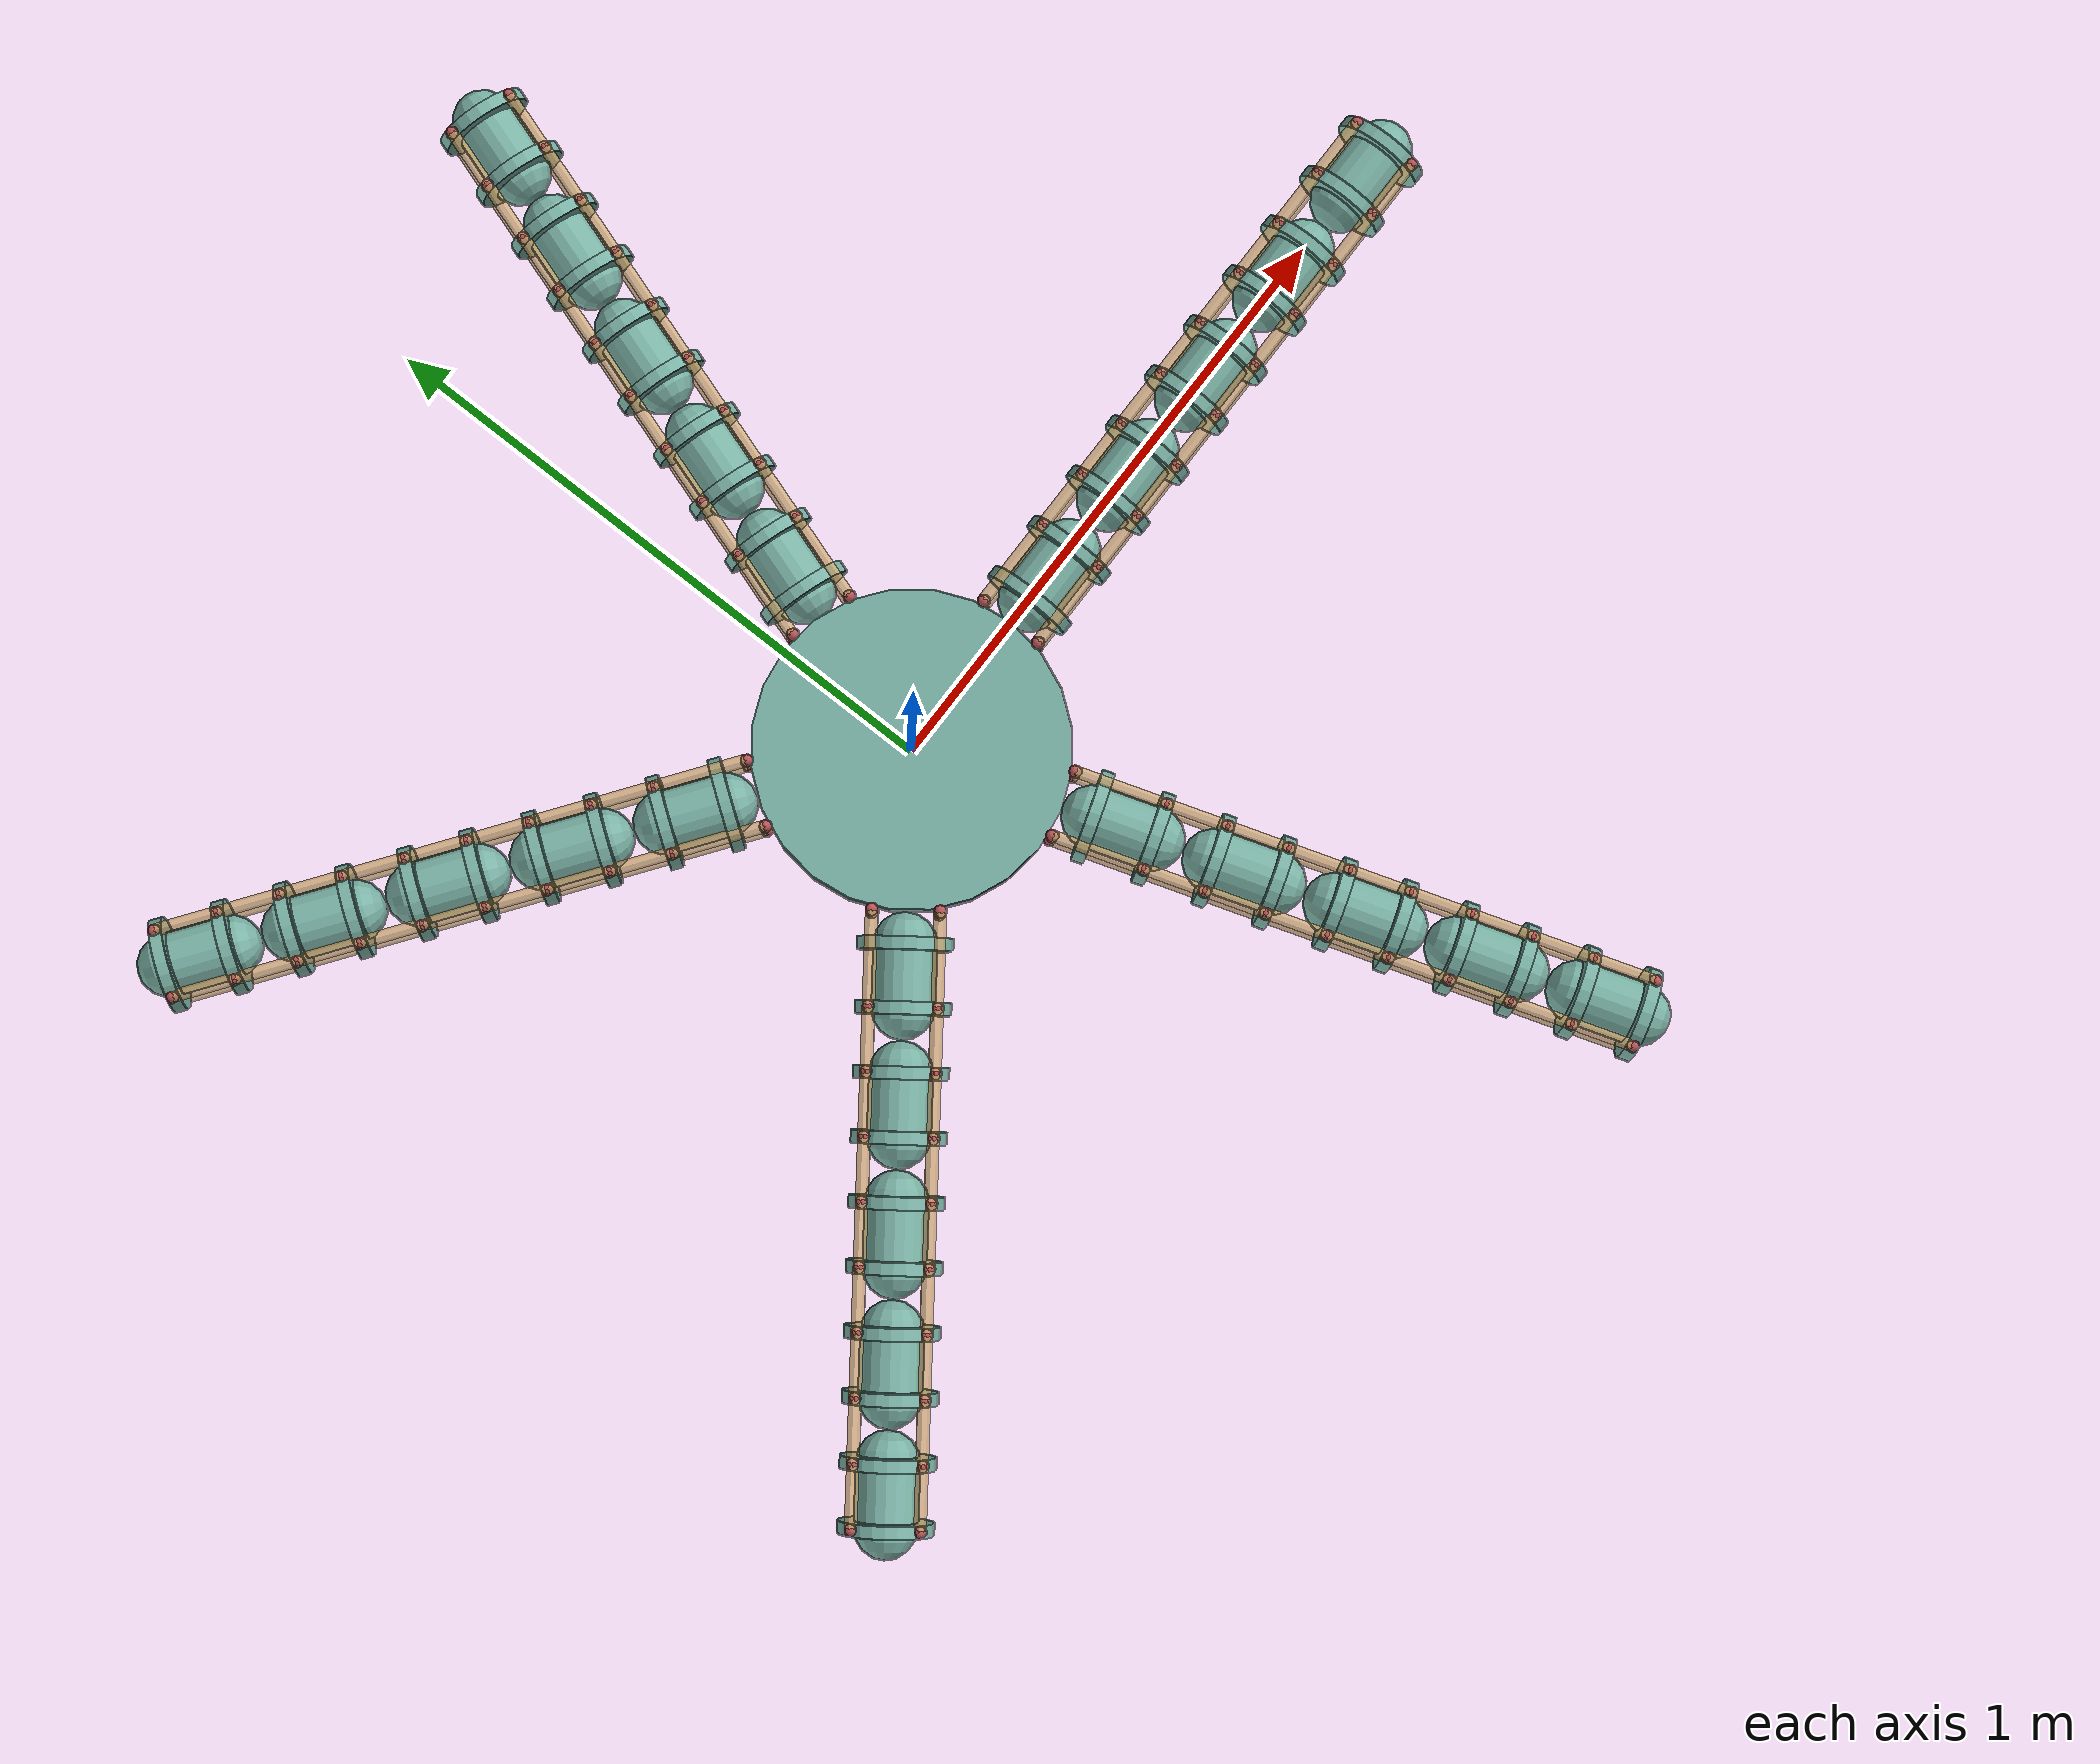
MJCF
<mujoco model="default">
  <compiler angle="radian"/>
  <default>
    <default class="/"/>
  </default>
  <worldbody>
    <body name="//unnamed_body_0">
      <body name="central_disc" pos="0 0 0" euler="0 0 0">
        <geom name="central_disc_disc" class="/" type="cylinder" size="0.25 0.050000000000000003" rgba="0.49019607843137253 0.70980392156862748 0.6588235294117647 1" pos="0 0 0" euler="0 0 0"/>
        <body name="arm_0" pos="0.25 0 0" euler="0 0 0">
          <body name="arm_0_segment_0" pos="0 0 0" euler="0 0 0">
            <geom name="arm_0_segment_0_capsule" class="/" type="capsule" size="0.050000000000000003 0.050000000000000003" rgba="0.49019607843137253 0.70980392156862748 0.6588235294117647 1" pos="0.10000000000000001 0 0" euler="0 1.5707963267948966 0"/>
            <joint name="arm_0_segment_0_in_plane_joint" class="/" type="hinge" pos="0 0 0" axis="0 0 1" limited="true" stiffness="100" range="-0.3490658503988659 0.3490658503988659" damping="10"/>
            <joint name="arm_0_segment_0_out_of_plane_joint" class="/" type="hinge" pos="0 0 0" axis="0 1 0" limited="true" stiffness="100" range="-0.3490658503988659 0.3490658503988659" damping="10"/>
            <geom name="arm_0_segment_0_tendon_plate_proximal" class="/" type="cylinder" size="0.075000000000000011 0.01" rgba="0.49019607843137253 0.70980392156862748 0.6588235294117647 1" pos="0.050000000000000003 0 0" euler="0 1.5707963267948966 0"/>
            <site name="arm_0_segment_0_muscle_attachment_point_proximal_0" class="/" type="sphere" rgba="0.71764705882352942 0.33725490196078434 0.34901960784313724 1" size="0.01" pos="0 0.053033008588991078 -0.053033008588991071"/>
            <site name="arm_0_segment_0_muscle_attachment_point_proximal_1" class="/" type="sphere" rgba="0.71764705882352942 0.33725490196078434 0.34901960784313724 1" size="0.01" pos="0 -0.053033008588991071 -0.053033008588991078"/>
            <site name="arm_0_segment_0_muscle_attachment_point_proximal_2" class="/" type="sphere" rgba="0.71764705882352942 0.33725490196078434 0.34901960784313724 1" size="0.01" pos="0 0.053033008588991078 0.053033008588991071"/>
            <site name="arm_0_segment_0_muscle_attachment_point_proximal_3" class="/" type="sphere" rgba="0.71764705882352942 0.33725490196078434 0.34901960784313724 1" size="0.01" pos="0 -0.053033008588991071 0.053033008588991078"/>
            <geom name="arm_0_segment_0_tendon_plate_distal" class="/" type="cylinder" size="0.075000000000000011 0.01" rgba="0.49019607843137253 0.70980392156862748 0.6588235294117647 1" pos="0.15000000000000002 0 0" euler="0 1.5707963267948966 0"/>
            <site name="arm_0_segment_0_muscle_attachment_point_distal_0" class="/" type="sphere" rgba="0.71764705882352942 0.33725490196078434 0.34901960784313724 1" size="0.01" pos="0.15000000000000002 0.053033008588991078 -0.053033008588991071"/>
            <site name="arm_0_segment_0_muscle_attachment_point_distal_1" class="/" type="sphere" rgba="0.71764705882352942 0.33725490196078434 0.34901960784313724 1" size="0.01" pos="0.15000000000000002 -0.053033008588991071 -0.053033008588991078"/>
            <site name="arm_0_segment_0_muscle_attachment_point_distal_2" class="/" type="sphere" rgba="0.71764705882352942 0.33725490196078434 0.34901960784313724 1" size="0.01" pos="0.15000000000000002 0.053033008588991078 0.053033008588991071"/>
            <site name="arm_0_segment_0_muscle_attachment_point_distal_3" class="/" type="sphere" rgba="0.71764705882352942 0.33725490196078434 0.34901960784313724 1" size="0.01" pos="0.15000000000000002 -0.053033008588991071 0.053033008588991078"/>
            <body name="arm_0_segment_1" pos="0.20000000000000001 0 0" euler="0 0 0">
              <geom name="arm_0_segment_1_capsule" class="/" type="capsule" size="0.050000000000000003 0.050000000000000003" rgba="0.49019607843137253 0.70980392156862748 0.6588235294117647 1" pos="0.10000000000000001 0 0" euler="0 1.5707963267948966 0"/>
              <joint name="arm_0_segment_1_in_plane_joint" class="/" type="hinge" pos="0 0 0" axis="0 0 1" limited="true" stiffness="100" range="-0.3490658503988659 0.3490658503988659" damping="10"/>
              <joint name="arm_0_segment_1_out_of_plane_joint" class="/" type="hinge" pos="0 0 0" axis="0 1 0" limited="true" stiffness="100" range="-0.3490658503988659 0.3490658503988659" damping="10"/>
              <geom name="arm_0_segment_1_tendon_plate_proximal" class="/" type="cylinder" size="0.075000000000000011 0.01" rgba="0.49019607843137253 0.70980392156862748 0.6588235294117647 1" pos="0.050000000000000003 0 0" euler="0 1.5707963267948966 0"/>
              <site name="arm_0_segment_1_muscle_attachment_point_proximal_0" class="/" type="sphere" rgba="0.71764705882352942 0.33725490196078434 0.34901960784313724 1" size="0.01" pos="0.050000000000000003 0.053033008588991078 -0.053033008588991071"/>
              <site name="arm_0_segment_1_muscle_attachment_point_proximal_1" class="/" type="sphere" rgba="0.71764705882352942 0.33725490196078434 0.34901960784313724 1" size="0.01" pos="0.050000000000000003 -0.053033008588991071 -0.053033008588991078"/>
              <site name="arm_0_segment_1_muscle_attachment_point_proximal_2" class="/" type="sphere" rgba="0.71764705882352942 0.33725490196078434 0.34901960784313724 1" size="0.01" pos="0.050000000000000003 0.053033008588991078 0.053033008588991071"/>
              <site name="arm_0_segment_1_muscle_attachment_point_proximal_3" class="/" type="sphere" rgba="0.71764705882352942 0.33725490196078434 0.34901960784313724 1" size="0.01" pos="0.050000000000000003 -0.053033008588991071 0.053033008588991078"/>
              <geom name="arm_0_segment_1_tendon_plate_distal" class="/" type="cylinder" size="0.075000000000000011 0.01" rgba="0.49019607843137253 0.70980392156862748 0.6588235294117647 1" pos="0.15000000000000002 0 0" euler="0 1.5707963267948966 0"/>
              <site name="arm_0_segment_1_muscle_attachment_point_distal_0" class="/" type="sphere" rgba="0.71764705882352942 0.33725490196078434 0.34901960784313724 1" size="0.01" pos="0.15000000000000002 0.053033008588991078 -0.053033008588991071"/>
              <site name="arm_0_segment_1_muscle_attachment_point_distal_1" class="/" type="sphere" rgba="0.71764705882352942 0.33725490196078434 0.34901960784313724 1" size="0.01" pos="0.15000000000000002 -0.053033008588991071 -0.053033008588991078"/>
              <site name="arm_0_segment_1_muscle_attachment_point_distal_2" class="/" type="sphere" rgba="0.71764705882352942 0.33725490196078434 0.34901960784313724 1" size="0.01" pos="0.15000000000000002 0.053033008588991078 0.053033008588991071"/>
              <site name="arm_0_segment_1_muscle_attachment_point_distal_3" class="/" type="sphere" rgba="0.71764705882352942 0.33725490196078434 0.34901960784313724 1" size="0.01" pos="0.15000000000000002 -0.053033008588991071 0.053033008588991078"/>
              <body name="arm_0_segment_2" pos="0.20000000000000001 0 0" euler="0 0 0">
                <geom name="arm_0_segment_2_capsule" class="/" type="capsule" size="0.050000000000000003 0.050000000000000003" rgba="0.49019607843137253 0.70980392156862748 0.6588235294117647 1" pos="0.10000000000000001 0 0" euler="0 1.5707963267948966 0"/>
                <joint name="arm_0_segment_2_in_plane_joint" class="/" type="hinge" pos="0 0 0" axis="0 0 1" limited="true" stiffness="100" range="-0.3490658503988659 0.3490658503988659" damping="10"/>
                <joint name="arm_0_segment_2_out_of_plane_joint" class="/" type="hinge" pos="0 0 0" axis="0 1 0" limited="true" stiffness="100" range="-0.3490658503988659 0.3490658503988659" damping="10"/>
                <geom name="arm_0_segment_2_tendon_plate_proximal" class="/" type="cylinder" size="0.075000000000000011 0.01" rgba="0.49019607843137253 0.70980392156862748 0.6588235294117647 1" pos="0.050000000000000003 0 0" euler="0 1.5707963267948966 0"/>
                <site name="arm_0_segment_2_muscle_attachment_point_proximal_0" class="/" type="sphere" rgba="0.71764705882352942 0.33725490196078434 0.34901960784313724 1" size="0.01" pos="0.050000000000000003 0.053033008588991078 -0.053033008588991071"/>
                <site name="arm_0_segment_2_muscle_attachment_point_proximal_1" class="/" type="sphere" rgba="0.71764705882352942 0.33725490196078434 0.34901960784313724 1" size="0.01" pos="0.050000000000000003 -0.053033008588991071 -0.053033008588991078"/>
                <site name="arm_0_segment_2_muscle_attachment_point_proximal_2" class="/" type="sphere" rgba="0.71764705882352942 0.33725490196078434 0.34901960784313724 1" size="0.01" pos="0.050000000000000003 0.053033008588991078 0.053033008588991071"/>
                <site name="arm_0_segment_2_muscle_attachment_point_proximal_3" class="/" type="sphere" rgba="0.71764705882352942 0.33725490196078434 0.34901960784313724 1" size="0.01" pos="0.050000000000000003 -0.053033008588991071 0.053033008588991078"/>
                <geom name="arm_0_segment_2_tendon_plate_distal" class="/" type="cylinder" size="0.075000000000000011 0.01" rgba="0.49019607843137253 0.70980392156862748 0.6588235294117647 1" pos="0.15000000000000002 0 0" euler="0 1.5707963267948966 0"/>
                <site name="arm_0_segment_2_muscle_attachment_point_distal_0" class="/" type="sphere" rgba="0.71764705882352942 0.33725490196078434 0.34901960784313724 1" size="0.01" pos="0.15000000000000002 0.053033008588991078 -0.053033008588991071"/>
                <site name="arm_0_segment_2_muscle_attachment_point_distal_1" class="/" type="sphere" rgba="0.71764705882352942 0.33725490196078434 0.34901960784313724 1" size="0.01" pos="0.15000000000000002 -0.053033008588991071 -0.053033008588991078"/>
                <site name="arm_0_segment_2_muscle_attachment_point_distal_2" class="/" type="sphere" rgba="0.71764705882352942 0.33725490196078434 0.34901960784313724 1" size="0.01" pos="0.15000000000000002 0.053033008588991078 0.053033008588991071"/>
                <site name="arm_0_segment_2_muscle_attachment_point_distal_3" class="/" type="sphere" rgba="0.71764705882352942 0.33725490196078434 0.34901960784313724 1" size="0.01" pos="0.15000000000000002 -0.053033008588991071 0.053033008588991078"/>
                <body name="arm_0_segment_3" pos="0.20000000000000001 0 0" euler="0 0 0">
                  <geom name="arm_0_segment_3_capsule" class="/" type="capsule" size="0.050000000000000003 0.050000000000000003" rgba="0.49019607843137253 0.70980392156862748 0.6588235294117647 1" pos="0.10000000000000001 0 0" euler="0 1.5707963267948966 0"/>
                  <joint name="arm_0_segment_3_in_plane_joint" class="/" type="hinge" pos="0 0 0" axis="0 0 1" limited="true" stiffness="100" range="-0.3490658503988659 0.3490658503988659" damping="10"/>
                  <joint name="arm_0_segment_3_out_of_plane_joint" class="/" type="hinge" pos="0 0 0" axis="0 1 0" limited="true" stiffness="100" range="-0.3490658503988659 0.3490658503988659" damping="10"/>
                  <geom name="arm_0_segment_3_tendon_plate_proximal" class="/" type="cylinder" size="0.075000000000000011 0.01" rgba="0.49019607843137253 0.70980392156862748 0.6588235294117647 1" pos="0.050000000000000003 0 0" euler="0 1.5707963267948966 0"/>
                  <site name="arm_0_segment_3_muscle_attachment_point_proximal_0" class="/" type="sphere" rgba="0.71764705882352942 0.33725490196078434 0.34901960784313724 1" size="0.01" pos="0.050000000000000003 0.053033008588991078 -0.053033008588991071"/>
                  <site name="arm_0_segment_3_muscle_attachment_point_proximal_1" class="/" type="sphere" rgba="0.71764705882352942 0.33725490196078434 0.34901960784313724 1" size="0.01" pos="0.050000000000000003 -0.053033008588991071 -0.053033008588991078"/>
                  <site name="arm_0_segment_3_muscle_attachment_point_proximal_2" class="/" type="sphere" rgba="0.71764705882352942 0.33725490196078434 0.34901960784313724 1" size="0.01" pos="0.050000000000000003 0.053033008588991078 0.053033008588991071"/>
                  <site name="arm_0_segment_3_muscle_attachment_point_proximal_3" class="/" type="sphere" rgba="0.71764705882352942 0.33725490196078434 0.34901960784313724 1" size="0.01" pos="0.050000000000000003 -0.053033008588991071 0.053033008588991078"/>
                  <geom name="arm_0_segment_3_tendon_plate_distal" class="/" type="cylinder" size="0.075000000000000011 0.01" rgba="0.49019607843137253 0.70980392156862748 0.6588235294117647 1" pos="0.15000000000000002 0 0" euler="0 1.5707963267948966 0"/>
                  <site name="arm_0_segment_3_muscle_attachment_point_distal_0" class="/" type="sphere" rgba="0.71764705882352942 0.33725490196078434 0.34901960784313724 1" size="0.01" pos="0.15000000000000002 0.053033008588991078 -0.053033008588991071"/>
                  <site name="arm_0_segment_3_muscle_attachment_point_distal_1" class="/" type="sphere" rgba="0.71764705882352942 0.33725490196078434 0.34901960784313724 1" size="0.01" pos="0.15000000000000002 -0.053033008588991071 -0.053033008588991078"/>
                  <site name="arm_0_segment_3_muscle_attachment_point_distal_2" class="/" type="sphere" rgba="0.71764705882352942 0.33725490196078434 0.34901960784313724 1" size="0.01" pos="0.15000000000000002 0.053033008588991078 0.053033008588991071"/>
                  <site name="arm_0_segment_3_muscle_attachment_point_distal_3" class="/" type="sphere" rgba="0.71764705882352942 0.33725490196078434 0.34901960784313724 1" size="0.01" pos="0.15000000000000002 -0.053033008588991071 0.053033008588991078"/>
                  <body name="arm_0_segment_4" pos="0.20000000000000001 0 0" euler="0 0 0">
                    <geom name="arm_0_segment_4_capsule" class="/" type="capsule" size="0.050000000000000003 0.050000000000000003" rgba="0.49019607843137253 0.70980392156862748 0.6588235294117647 1" pos="0.10000000000000001 0 0" euler="0 1.5707963267948966 0"/>
                    <joint name="arm_0_segment_4_in_plane_joint" class="/" type="hinge" pos="0 0 0" axis="0 0 1" limited="true" stiffness="100" range="-0.3490658503988659 0.3490658503988659" damping="10"/>
                    <joint name="arm_0_segment_4_out_of_plane_joint" class="/" type="hinge" pos="0 0 0" axis="0 1 0" limited="true" stiffness="100" range="-0.3490658503988659 0.3490658503988659" damping="10"/>
                    <geom name="arm_0_segment_4_tendon_plate_proximal" class="/" type="cylinder" size="0.075000000000000011 0.01" rgba="0.49019607843137253 0.70980392156862748 0.6588235294117647 1" pos="0.050000000000000003 0 0" euler="0 1.5707963267948966 0"/>
                    <site name="arm_0_segment_4_muscle_attachment_point_proximal_0" class="/" type="sphere" rgba="0.71764705882352942 0.33725490196078434 0.34901960784313724 1" size="0.01" pos="0.050000000000000003 0.053033008588991078 -0.053033008588991071"/>
                    <site name="arm_0_segment_4_muscle_attachment_point_proximal_1" class="/" type="sphere" rgba="0.71764705882352942 0.33725490196078434 0.34901960784313724 1" size="0.01" pos="0.050000000000000003 -0.053033008588991071 -0.053033008588991078"/>
                    <site name="arm_0_segment_4_muscle_attachment_point_proximal_2" class="/" type="sphere" rgba="0.71764705882352942 0.33725490196078434 0.34901960784313724 1" size="0.01" pos="0.050000000000000003 0.053033008588991078 0.053033008588991071"/>
                    <site name="arm_0_segment_4_muscle_attachment_point_proximal_3" class="/" type="sphere" rgba="0.71764705882352942 0.33725490196078434 0.34901960784313724 1" size="0.01" pos="0.050000000000000003 -0.053033008588991071 0.053033008588991078"/>
                    <geom name="arm_0_segment_4_tendon_plate_distal" class="/" type="cylinder" size="0.075000000000000011 0.01" rgba="0.49019607843137253 0.70980392156862748 0.6588235294117647 1" pos="0.15000000000000002 0 0" euler="0 1.5707963267948966 0"/>
                    <site name="arm_0_segment_4_muscle_attachment_point_distal_0" class="/" type="sphere" rgba="0.71764705882352942 0.33725490196078434 0.34901960784313724 1" size="0.01" pos="0.15000000000000002 0.053033008588991078 -0.053033008588991071"/>
                    <site name="arm_0_segment_4_muscle_attachment_point_distal_1" class="/" type="sphere" rgba="0.71764705882352942 0.33725490196078434 0.34901960784313724 1" size="0.01" pos="0.15000000000000002 -0.053033008588991071 -0.053033008588991078"/>
                    <site name="arm_0_segment_4_muscle_attachment_point_distal_2" class="/" type="sphere" rgba="0.71764705882352942 0.33725490196078434 0.34901960784313724 1" size="0.01" pos="0.15000000000000002 0.053033008588991078 0.053033008588991071"/>
                    <site name="arm_0_segment_4_muscle_attachment_point_distal_3" class="/" type="sphere" rgba="0.71764705882352942 0.33725490196078434 0.34901960784313724 1" size="0.01" pos="0.15000000000000002 -0.053033008588991071 0.053033008588991078"/>
                  </body>
                </body>
              </body>
            </body>
          </body>
          <site name="arm_0_muscle_attachment_point_0" class="/" type="sphere" rgba="0.71764705882352942 0.33725490196078434 0.34901960784313724 1" size="0.01" pos="0 0.053033008588991078 -0.053033008588991071"/>
          <site name="arm_0_muscle_attachment_point_1" class="/" type="sphere" rgba="0.71764705882352942 0.33725490196078434 0.34901960784313724 1" size="0.01" pos="0 -0.053033008588991071 -0.053033008588991078"/>
          <site name="arm_0_muscle_attachment_point_2" class="/" type="sphere" rgba="0.71764705882352942 0.33725490196078434 0.34901960784313724 1" size="0.01" pos="0 0.053033008588991078 0.053033008588991071"/>
          <site name="arm_0_muscle_attachment_point_3" class="/" type="sphere" rgba="0.71764705882352942 0.33725490196078434 0.34901960784313724 1" size="0.01" pos="0 -0.053033008588991071 0.053033008588991078"/>
        </body>
        <body name="arm_1" pos="0.077254248593736863 0.23776412907378838 0" euler="0 0 1.2566370614359172">
          <body name="arm_1_segment_0" pos="0 0 0" euler="0 0 0">
            <geom name="arm_1_segment_0_capsule" class="/" type="capsule" size="0.050000000000000003 0.050000000000000003" rgba="0.49019607843137253 0.70980392156862748 0.6588235294117647 1" pos="0.10000000000000001 0 0" euler="0 1.5707963267948966 0"/>
            <joint name="arm_1_segment_0_in_plane_joint" class="/" type="hinge" pos="0 0 0" axis="0 0 1" limited="true" stiffness="100" range="-0.3490658503988659 0.3490658503988659" damping="10"/>
            <joint name="arm_1_segment_0_out_of_plane_joint" class="/" type="hinge" pos="0 0 0" axis="0 1 0" limited="true" stiffness="100" range="-0.3490658503988659 0.3490658503988659" damping="10"/>
            <geom name="arm_1_segment_0_tendon_plate_proximal" class="/" type="cylinder" size="0.075000000000000011 0.01" rgba="0.49019607843137253 0.70980392156862748 0.6588235294117647 1" pos="0.050000000000000003 0 0" euler="0 1.5707963267948966 0"/>
            <site name="arm_1_segment_0_muscle_attachment_point_proximal_0" class="/" type="sphere" rgba="0.71764705882352942 0.33725490196078434 0.34901960784313724 1" size="0.01" pos="0 0.053033008588991078 -0.053033008588991071"/>
            <site name="arm_1_segment_0_muscle_attachment_point_proximal_1" class="/" type="sphere" rgba="0.71764705882352942 0.33725490196078434 0.34901960784313724 1" size="0.01" pos="0 -0.053033008588991071 -0.053033008588991078"/>
            <site name="arm_1_segment_0_muscle_attachment_point_proximal_2" class="/" type="sphere" rgba="0.71764705882352942 0.33725490196078434 0.34901960784313724 1" size="0.01" pos="0 0.053033008588991078 0.053033008588991071"/>
            <site name="arm_1_segment_0_muscle_attachment_point_proximal_3" class="/" type="sphere" rgba="0.71764705882352942 0.33725490196078434 0.34901960784313724 1" size="0.01" pos="0 -0.053033008588991071 0.053033008588991078"/>
            <geom name="arm_1_segment_0_tendon_plate_distal" class="/" type="cylinder" size="0.075000000000000011 0.01" rgba="0.49019607843137253 0.70980392156862748 0.6588235294117647 1" pos="0.15000000000000002 0 0" euler="0 1.5707963267948966 0"/>
            <site name="arm_1_segment_0_muscle_attachment_point_distal_0" class="/" type="sphere" rgba="0.71764705882352942 0.33725490196078434 0.34901960784313724 1" size="0.01" pos="0.15000000000000002 0.053033008588991078 -0.053033008588991071"/>
            <site name="arm_1_segment_0_muscle_attachment_point_distal_1" class="/" type="sphere" rgba="0.71764705882352942 0.33725490196078434 0.34901960784313724 1" size="0.01" pos="0.15000000000000002 -0.053033008588991071 -0.053033008588991078"/>
            <site name="arm_1_segment_0_muscle_attachment_point_distal_2" class="/" type="sphere" rgba="0.71764705882352942 0.33725490196078434 0.34901960784313724 1" size="0.01" pos="0.15000000000000002 0.053033008588991078 0.053033008588991071"/>
            <site name="arm_1_segment_0_muscle_attachment_point_distal_3" class="/" type="sphere" rgba="0.71764705882352942 0.33725490196078434 0.34901960784313724 1" size="0.01" pos="0.15000000000000002 -0.053033008588991071 0.053033008588991078"/>
            <body name="arm_1_segment_1" pos="0.20000000000000001 0 0" euler="0 0 0">
              <geom name="arm_1_segment_1_capsule" class="/" type="capsule" size="0.050000000000000003 0.050000000000000003" rgba="0.49019607843137253 0.70980392156862748 0.6588235294117647 1" pos="0.10000000000000001 0 0" euler="0 1.5707963267948966 0"/>
              <joint name="arm_1_segment_1_in_plane_joint" class="/" type="hinge" pos="0 0 0" axis="0 0 1" limited="true" stiffness="100" range="-0.3490658503988659 0.3490658503988659" damping="10"/>
              <joint name="arm_1_segment_1_out_of_plane_joint" class="/" type="hinge" pos="0 0 0" axis="0 1 0" limited="true" stiffness="100" range="-0.3490658503988659 0.3490658503988659" damping="10"/>
              <geom name="arm_1_segment_1_tendon_plate_proximal" class="/" type="cylinder" size="0.075000000000000011 0.01" rgba="0.49019607843137253 0.70980392156862748 0.6588235294117647 1" pos="0.050000000000000003 0 0" euler="0 1.5707963267948966 0"/>
              <site name="arm_1_segment_1_muscle_attachment_point_proximal_0" class="/" type="sphere" rgba="0.71764705882352942 0.33725490196078434 0.34901960784313724 1" size="0.01" pos="0.050000000000000003 0.053033008588991078 -0.053033008588991071"/>
              <site name="arm_1_segment_1_muscle_attachment_point_proximal_1" class="/" type="sphere" rgba="0.71764705882352942 0.33725490196078434 0.34901960784313724 1" size="0.01" pos="0.050000000000000003 -0.053033008588991071 -0.053033008588991078"/>
              <site name="arm_1_segment_1_muscle_attachment_point_proximal_2" class="/" type="sphere" rgba="0.71764705882352942 0.33725490196078434 0.34901960784313724 1" size="0.01" pos="0.050000000000000003 0.053033008588991078 0.053033008588991071"/>
              <site name="arm_1_segment_1_muscle_attachment_point_proximal_3" class="/" type="sphere" rgba="0.71764705882352942 0.33725490196078434 0.34901960784313724 1" size="0.01" pos="0.050000000000000003 -0.053033008588991071 0.053033008588991078"/>
              <geom name="arm_1_segment_1_tendon_plate_distal" class="/" type="cylinder" size="0.075000000000000011 0.01" rgba="0.49019607843137253 0.70980392156862748 0.6588235294117647 1" pos="0.15000000000000002 0 0" euler="0 1.5707963267948966 0"/>
              <site name="arm_1_segment_1_muscle_attachment_point_distal_0" class="/" type="sphere" rgba="0.71764705882352942 0.33725490196078434 0.34901960784313724 1" size="0.01" pos="0.15000000000000002 0.053033008588991078 -0.053033008588991071"/>
              <site name="arm_1_segment_1_muscle_attachment_point_distal_1" class="/" type="sphere" rgba="0.71764705882352942 0.33725490196078434 0.34901960784313724 1" size="0.01" pos="0.15000000000000002 -0.053033008588991071 -0.053033008588991078"/>
              <site name="arm_1_segment_1_muscle_attachment_point_distal_2" class="/" type="sphere" rgba="0.71764705882352942 0.33725490196078434 0.34901960784313724 1" size="0.01" pos="0.15000000000000002 0.053033008588991078 0.053033008588991071"/>
              <site name="arm_1_segment_1_muscle_attachment_point_distal_3" class="/" type="sphere" rgba="0.71764705882352942 0.33725490196078434 0.34901960784313724 1" size="0.01" pos="0.15000000000000002 -0.053033008588991071 0.053033008588991078"/>
              <body name="arm_1_segment_2" pos="0.20000000000000001 0 0" euler="0 0 0">
                <geom name="arm_1_segment_2_capsule" class="/" type="capsule" size="0.050000000000000003 0.050000000000000003" rgba="0.49019607843137253 0.70980392156862748 0.6588235294117647 1" pos="0.10000000000000001 0 0" euler="0 1.5707963267948966 0"/>
                <joint name="arm_1_segment_2_in_plane_joint" class="/" type="hinge" pos="0 0 0" axis="0 0 1" limited="true" stiffness="100" range="-0.3490658503988659 0.3490658503988659" damping="10"/>
                <joint name="arm_1_segment_2_out_of_plane_joint" class="/" type="hinge" pos="0 0 0" axis="0 1 0" limited="true" stiffness="100" range="-0.3490658503988659 0.3490658503988659" damping="10"/>
                <geom name="arm_1_segment_2_tendon_plate_proximal" class="/" type="cylinder" size="0.075000000000000011 0.01" rgba="0.49019607843137253 0.70980392156862748 0.6588235294117647 1" pos="0.050000000000000003 0 0" euler="0 1.5707963267948966 0"/>
                <site name="arm_1_segment_2_muscle_attachment_point_proximal_0" class="/" type="sphere" rgba="0.71764705882352942 0.33725490196078434 0.34901960784313724 1" size="0.01" pos="0.050000000000000003 0.053033008588991078 -0.053033008588991071"/>
                <site name="arm_1_segment_2_muscle_attachment_point_proximal_1" class="/" type="sphere" rgba="0.71764705882352942 0.33725490196078434 0.34901960784313724 1" size="0.01" pos="0.050000000000000003 -0.053033008588991071 -0.053033008588991078"/>
                <site name="arm_1_segment_2_muscle_attachment_point_proximal_2" class="/" type="sphere" rgba="0.71764705882352942 0.33725490196078434 0.34901960784313724 1" size="0.01" pos="0.050000000000000003 0.053033008588991078 0.053033008588991071"/>
                <site name="arm_1_segment_2_muscle_attachment_point_proximal_3" class="/" type="sphere" rgba="0.71764705882352942 0.33725490196078434 0.34901960784313724 1" size="0.01" pos="0.050000000000000003 -0.053033008588991071 0.053033008588991078"/>
                <geom name="arm_1_segment_2_tendon_plate_distal" class="/" type="cylinder" size="0.075000000000000011 0.01" rgba="0.49019607843137253 0.70980392156862748 0.6588235294117647 1" pos="0.15000000000000002 0 0" euler="0 1.5707963267948966 0"/>
                <site name="arm_1_segment_2_muscle_attachment_point_distal_0" class="/" type="sphere" rgba="0.71764705882352942 0.33725490196078434 0.34901960784313724 1" size="0.01" pos="0.15000000000000002 0.053033008588991078 -0.053033008588991071"/>
                <site name="arm_1_segment_2_muscle_attachment_point_distal_1" class="/" type="sphere" rgba="0.71764705882352942 0.33725490196078434 0.34901960784313724 1" size="0.01" pos="0.15000000000000002 -0.053033008588991071 -0.053033008588991078"/>
                <site name="arm_1_segment_2_muscle_attachment_point_distal_2" class="/" type="sphere" rgba="0.71764705882352942 0.33725490196078434 0.34901960784313724 1" size="0.01" pos="0.15000000000000002 0.053033008588991078 0.053033008588991071"/>
                <site name="arm_1_segment_2_muscle_attachment_point_distal_3" class="/" type="sphere" rgba="0.71764705882352942 0.33725490196078434 0.34901960784313724 1" size="0.01" pos="0.15000000000000002 -0.053033008588991071 0.053033008588991078"/>
                <body name="arm_1_segment_3" pos="0.20000000000000001 0 0" euler="0 0 0">
                  <geom name="arm_1_segment_3_capsule" class="/" type="capsule" size="0.050000000000000003 0.050000000000000003" rgba="0.49019607843137253 0.70980392156862748 0.6588235294117647 1" pos="0.10000000000000001 0 0" euler="0 1.5707963267948966 0"/>
                  <joint name="arm_1_segment_3_in_plane_joint" class="/" type="hinge" pos="0 0 0" axis="0 0 1" limited="true" stiffness="100" range="-0.3490658503988659 0.3490658503988659" damping="10"/>
                  <joint name="arm_1_segment_3_out_of_plane_joint" class="/" type="hinge" pos="0 0 0" axis="0 1 0" limited="true" stiffness="100" range="-0.3490658503988659 0.3490658503988659" damping="10"/>
                  <geom name="arm_1_segment_3_tendon_plate_proximal" class="/" type="cylinder" size="0.075000000000000011 0.01" rgba="0.49019607843137253 0.70980392156862748 0.6588235294117647 1" pos="0.050000000000000003 0 0" euler="0 1.5707963267948966 0"/>
                  <site name="arm_1_segment_3_muscle_attachment_point_proximal_0" class="/" type="sphere" rgba="0.71764705882352942 0.33725490196078434 0.34901960784313724 1" size="0.01" pos="0.050000000000000003 0.053033008588991078 -0.053033008588991071"/>
                  <site name="arm_1_segment_3_muscle_attachment_point_proximal_1" class="/" type="sphere" rgba="0.71764705882352942 0.33725490196078434 0.34901960784313724 1" size="0.01" pos="0.050000000000000003 -0.053033008588991071 -0.053033008588991078"/>
                  <site name="arm_1_segment_3_muscle_attachment_point_proximal_2" class="/" type="sphere" rgba="0.71764705882352942 0.33725490196078434 0.34901960784313724 1" size="0.01" pos="0.050000000000000003 0.053033008588991078 0.053033008588991071"/>
                  <site name="arm_1_segment_3_muscle_attachment_point_proximal_3" class="/" type="sphere" rgba="0.71764705882352942 0.33725490196078434 0.34901960784313724 1" size="0.01" pos="0.050000000000000003 -0.053033008588991071 0.053033008588991078"/>
                  <geom name="arm_1_segment_3_tendon_plate_distal" class="/" type="cylinder" size="0.075000000000000011 0.01" rgba="0.49019607843137253 0.70980392156862748 0.6588235294117647 1" pos="0.15000000000000002 0 0" euler="0 1.5707963267948966 0"/>
                  <site name="arm_1_segment_3_muscle_attachment_point_distal_0" class="/" type="sphere" rgba="0.71764705882352942 0.33725490196078434 0.34901960784313724 1" size="0.01" pos="0.15000000000000002 0.053033008588991078 -0.053033008588991071"/>
                  <site name="arm_1_segment_3_muscle_attachment_point_distal_1" class="/" type="sphere" rgba="0.71764705882352942 0.33725490196078434 0.34901960784313724 1" size="0.01" pos="0.15000000000000002 -0.053033008588991071 -0.053033008588991078"/>
                  <site name="arm_1_segment_3_muscle_attachment_point_distal_2" class="/" type="sphere" rgba="0.71764705882352942 0.33725490196078434 0.34901960784313724 1" size="0.01" pos="0.15000000000000002 0.053033008588991078 0.053033008588991071"/>
                  <site name="arm_1_segment_3_muscle_attachment_point_distal_3" class="/" type="sphere" rgba="0.71764705882352942 0.33725490196078434 0.34901960784313724 1" size="0.01" pos="0.15000000000000002 -0.053033008588991071 0.053033008588991078"/>
                  <body name="arm_1_segment_4" pos="0.20000000000000001 0 0" euler="0 0 0">
                    <geom name="arm_1_segment_4_capsule" class="/" type="capsule" size="0.050000000000000003 0.050000000000000003" rgba="0.49019607843137253 0.70980392156862748 0.6588235294117647 1" pos="0.10000000000000001 0 0" euler="0 1.5707963267948966 0"/>
                    <joint name="arm_1_segment_4_in_plane_joint" class="/" type="hinge" pos="0 0 0" axis="0 0 1" limited="true" stiffness="100" range="-0.3490658503988659 0.3490658503988659" damping="10"/>
                    <joint name="arm_1_segment_4_out_of_plane_joint" class="/" type="hinge" pos="0 0 0" axis="0 1 0" limited="true" stiffness="100" range="-0.3490658503988659 0.3490658503988659" damping="10"/>
                    <geom name="arm_1_segment_4_tendon_plate_proximal" class="/" type="cylinder" size="0.075000000000000011 0.01" rgba="0.49019607843137253 0.70980392156862748 0.6588235294117647 1" pos="0.050000000000000003 0 0" euler="0 1.5707963267948966 0"/>
                    <site name="arm_1_segment_4_muscle_attachment_point_proximal_0" class="/" type="sphere" rgba="0.71764705882352942 0.33725490196078434 0.34901960784313724 1" size="0.01" pos="0.050000000000000003 0.053033008588991078 -0.053033008588991071"/>
                    <site name="arm_1_segment_4_muscle_attachment_point_proximal_1" class="/" type="sphere" rgba="0.71764705882352942 0.33725490196078434 0.34901960784313724 1" size="0.01" pos="0.050000000000000003 -0.053033008588991071 -0.053033008588991078"/>
                    <site name="arm_1_segment_4_muscle_attachment_point_proximal_2" class="/" type="sphere" rgba="0.71764705882352942 0.33725490196078434 0.34901960784313724 1" size="0.01" pos="0.050000000000000003 0.053033008588991078 0.053033008588991071"/>
                    <site name="arm_1_segment_4_muscle_attachment_point_proximal_3" class="/" type="sphere" rgba="0.71764705882352942 0.33725490196078434 0.34901960784313724 1" size="0.01" pos="0.050000000000000003 -0.053033008588991071 0.053033008588991078"/>
                    <geom name="arm_1_segment_4_tendon_plate_distal" class="/" type="cylinder" size="0.075000000000000011 0.01" rgba="0.49019607843137253 0.70980392156862748 0.6588235294117647 1" pos="0.15000000000000002 0 0" euler="0 1.5707963267948966 0"/>
                    <site name="arm_1_segment_4_muscle_attachment_point_distal_0" class="/" type="sphere" rgba="0.71764705882352942 0.33725490196078434 0.34901960784313724 1" size="0.01" pos="0.15000000000000002 0.053033008588991078 -0.053033008588991071"/>
                    <site name="arm_1_segment_4_muscle_attachment_point_distal_1" class="/" type="sphere" rgba="0.71764705882352942 0.33725490196078434 0.34901960784313724 1" size="0.01" pos="0.15000000000000002 -0.053033008588991071 -0.053033008588991078"/>
                    <site name="arm_1_segment_4_muscle_attachment_point_distal_2" class="/" type="sphere" rgba="0.71764705882352942 0.33725490196078434 0.34901960784313724 1" size="0.01" pos="0.15000000000000002 0.053033008588991078 0.053033008588991071"/>
                    <site name="arm_1_segment_4_muscle_attachment_point_distal_3" class="/" type="sphere" rgba="0.71764705882352942 0.33725490196078434 0.34901960784313724 1" size="0.01" pos="0.15000000000000002 -0.053033008588991071 0.053033008588991078"/>
                  </body>
                </body>
              </body>
            </body>
          </body>
          <site name="arm_1_muscle_attachment_point_0" class="/" type="sphere" rgba="0.71764705882352942 0.33725490196078434 0.34901960784313724 1" size="0.01" pos="0 0.053033008588991078 -0.053033008588991071"/>
          <site name="arm_1_muscle_attachment_point_1" class="/" type="sphere" rgba="0.71764705882352942 0.33725490196078434 0.34901960784313724 1" size="0.01" pos="0 -0.053033008588991071 -0.053033008588991078"/>
          <site name="arm_1_muscle_attachment_point_2" class="/" type="sphere" rgba="0.71764705882352942 0.33725490196078434 0.34901960784313724 1" size="0.01" pos="0 0.053033008588991078 0.053033008588991071"/>
          <site name="arm_1_muscle_attachment_point_3" class="/" type="sphere" rgba="0.71764705882352942 0.33725490196078434 0.34901960784313724 1" size="0.01" pos="0 -0.053033008588991071 0.053033008588991078"/>
        </body>
        <body name="arm_2" pos="-0.20225424859373684 0.14694631307311831 0" euler="0 0 2.5132741228718345">
          <body name="arm_2_segment_0" pos="0 0 0" euler="0 0 0">
            <geom name="arm_2_segment_0_capsule" class="/" type="capsule" size="0.050000000000000003 0.050000000000000003" rgba="0.49019607843137253 0.70980392156862748 0.6588235294117647 1" pos="0.10000000000000001 0 0" euler="0 1.5707963267948966 0"/>
            <joint name="arm_2_segment_0_in_plane_joint" class="/" type="hinge" pos="0 0 0" axis="0 0 1" limited="true" stiffness="100" range="-0.3490658503988659 0.3490658503988659" damping="10"/>
            <joint name="arm_2_segment_0_out_of_plane_joint" class="/" type="hinge" pos="0 0 0" axis="0 1 0" limited="true" stiffness="100" range="-0.3490658503988659 0.3490658503988659" damping="10"/>
            <geom name="arm_2_segment_0_tendon_plate_proximal" class="/" type="cylinder" size="0.075000000000000011 0.01" rgba="0.49019607843137253 0.70980392156862748 0.6588235294117647 1" pos="0.050000000000000003 0 0" euler="0 1.5707963267948966 0"/>
            <site name="arm_2_segment_0_muscle_attachment_point_proximal_0" class="/" type="sphere" rgba="0.71764705882352942 0.33725490196078434 0.34901960784313724 1" size="0.01" pos="0 0.053033008588991078 -0.053033008588991071"/>
            <site name="arm_2_segment_0_muscle_attachment_point_proximal_1" class="/" type="sphere" rgba="0.71764705882352942 0.33725490196078434 0.34901960784313724 1" size="0.01" pos="0 -0.053033008588991071 -0.053033008588991078"/>
            <site name="arm_2_segment_0_muscle_attachment_point_proximal_2" class="/" type="sphere" rgba="0.71764705882352942 0.33725490196078434 0.34901960784313724 1" size="0.01" pos="0 0.053033008588991078 0.053033008588991071"/>
            <site name="arm_2_segment_0_muscle_attachment_point_proximal_3" class="/" type="sphere" rgba="0.71764705882352942 0.33725490196078434 0.34901960784313724 1" size="0.01" pos="0 -0.053033008588991071 0.053033008588991078"/>
            <geom name="arm_2_segment_0_tendon_plate_distal" class="/" type="cylinder" size="0.075000000000000011 0.01" rgba="0.49019607843137253 0.70980392156862748 0.6588235294117647 1" pos="0.15000000000000002 0 0" euler="0 1.5707963267948966 0"/>
            <site name="arm_2_segment_0_muscle_attachment_point_distal_0" class="/" type="sphere" rgba="0.71764705882352942 0.33725490196078434 0.34901960784313724 1" size="0.01" pos="0.15000000000000002 0.053033008588991078 -0.053033008588991071"/>
            <site name="arm_2_segment_0_muscle_attachment_point_distal_1" class="/" type="sphere" rgba="0.71764705882352942 0.33725490196078434 0.34901960784313724 1" size="0.01" pos="0.15000000000000002 -0.053033008588991071 -0.053033008588991078"/>
            <site name="arm_2_segment_0_muscle_attachment_point_distal_2" class="/" type="sphere" rgba="0.71764705882352942 0.33725490196078434 0.34901960784313724 1" size="0.01" pos="0.15000000000000002 0.053033008588991078 0.053033008588991071"/>
            <site name="arm_2_segment_0_muscle_attachment_point_distal_3" class="/" type="sphere" rgba="0.71764705882352942 0.33725490196078434 0.34901960784313724 1" size="0.01" pos="0.15000000000000002 -0.053033008588991071 0.053033008588991078"/>
            <body name="arm_2_segment_1" pos="0.20000000000000001 0 0" euler="0 0 0">
              <geom name="arm_2_segment_1_capsule" class="/" type="capsule" size="0.050000000000000003 0.050000000000000003" rgba="0.49019607843137253 0.70980392156862748 0.6588235294117647 1" pos="0.10000000000000001 0 0" euler="0 1.5707963267948966 0"/>
              <joint name="arm_2_segment_1_in_plane_joint" class="/" type="hinge" pos="0 0 0" axis="0 0 1" limited="true" stiffness="100" range="-0.3490658503988659 0.3490658503988659" damping="10"/>
              <joint name="arm_2_segment_1_out_of_plane_joint" class="/" type="hinge" pos="0 0 0" axis="0 1 0" limited="true" stiffness="100" range="-0.3490658503988659 0.3490658503988659" damping="10"/>
              <geom name="arm_2_segment_1_tendon_plate_proximal" class="/" type="cylinder" size="0.075000000000000011 0.01" rgba="0.49019607843137253 0.70980392156862748 0.6588235294117647 1" pos="0.050000000000000003 0 0" euler="0 1.5707963267948966 0"/>
              <site name="arm_2_segment_1_muscle_attachment_point_proximal_0" class="/" type="sphere" rgba="0.71764705882352942 0.33725490196078434 0.34901960784313724 1" size="0.01" pos="0.050000000000000003 0.053033008588991078 -0.053033008588991071"/>
              <site name="arm_2_segment_1_muscle_attachment_point_proximal_1" class="/" type="sphere" rgba="0.71764705882352942 0.33725490196078434 0.34901960784313724 1" size="0.01" pos="0.050000000000000003 -0.053033008588991071 -0.053033008588991078"/>
              <site name="arm_2_segment_1_muscle_attachment_point_proximal_2" class="/" type="sphere" rgba="0.71764705882352942 0.33725490196078434 0.34901960784313724 1" size="0.01" pos="0.050000000000000003 0.053033008588991078 0.053033008588991071"/>
              <site name="arm_2_segment_1_muscle_attachment_point_proximal_3" class="/" type="sphere" rgba="0.71764705882352942 0.33725490196078434 0.34901960784313724 1" size="0.01" pos="0.050000000000000003 -0.053033008588991071 0.053033008588991078"/>
              <geom name="arm_2_segment_1_tendon_plate_distal" class="/" type="cylinder" size="0.075000000000000011 0.01" rgba="0.49019607843137253 0.70980392156862748 0.6588235294117647 1" pos="0.15000000000000002 0 0" euler="0 1.5707963267948966 0"/>
              <site name="arm_2_segment_1_muscle_attachment_point_distal_0" class="/" type="sphere" rgba="0.71764705882352942 0.33725490196078434 0.34901960784313724 1" size="0.01" pos="0.15000000000000002 0.053033008588991078 -0.053033008588991071"/>
              <site name="arm_2_segment_1_muscle_attachment_point_distal_1" class="/" type="sphere" rgba="0.71764705882352942 0.33725490196078434 0.34901960784313724 1" size="0.01" pos="0.15000000000000002 -0.053033008588991071 -0.053033008588991078"/>
              <site name="arm_2_segment_1_muscle_attachment_point_distal_2" class="/" type="sphere" rgba="0.71764705882352942 0.33725490196078434 0.34901960784313724 1" size="0.01" pos="0.15000000000000002 0.053033008588991078 0.053033008588991071"/>
              <site name="arm_2_segment_1_muscle_attachment_point_distal_3" class="/" type="sphere" rgba="0.71764705882352942 0.33725490196078434 0.34901960784313724 1" size="0.01" pos="0.15000000000000002 -0.053033008588991071 0.053033008588991078"/>
              <body name="arm_2_segment_2" pos="0.20000000000000001 0 0" euler="0 0 0">
                <geom name="arm_2_segment_2_capsule" class="/" type="capsule" size="0.050000000000000003 0.050000000000000003" rgba="0.49019607843137253 0.70980392156862748 0.6588235294117647 1" pos="0.10000000000000001 0 0" euler="0 1.5707963267948966 0"/>
                <joint name="arm_2_segment_2_in_plane_joint" class="/" type="hinge" pos="0 0 0" axis="0 0 1" limited="true" stiffness="100" range="-0.3490658503988659 0.3490658503988659" damping="10"/>
                <joint name="arm_2_segment_2_out_of_plane_joint" class="/" type="hinge" pos="0 0 0" axis="0 1 0" limited="true" stiffness="100" range="-0.3490658503988659 0.3490658503988659" damping="10"/>
                <geom name="arm_2_segment_2_tendon_plate_proximal" class="/" type="cylinder" size="0.075000000000000011 0.01" rgba="0.49019607843137253 0.70980392156862748 0.6588235294117647 1" pos="0.050000000000000003 0 0" euler="0 1.5707963267948966 0"/>
                <site name="arm_2_segment_2_muscle_attachment_point_proximal_0" class="/" type="sphere" rgba="0.71764705882352942 0.33725490196078434 0.34901960784313724 1" size="0.01" pos="0.050000000000000003 0.053033008588991078 -0.053033008588991071"/>
                <site name="arm_2_segment_2_muscle_attachment_point_proximal_1" class="/" type="sphere" rgba="0.71764705882352942 0.33725490196078434 0.34901960784313724 1" size="0.01" pos="0.050000000000000003 -0.053033008588991071 -0.053033008588991078"/>
                <site name="arm_2_segment_2_muscle_attachment_point_proximal_2" class="/" type="sphere" rgba="0.71764705882352942 0.33725490196078434 0.34901960784313724 1" size="0.01" pos="0.050000000000000003 0.053033008588991078 0.053033008588991071"/>
                <site name="arm_2_segment_2_muscle_attachment_point_proximal_3" class="/" type="sphere" rgba="0.71764705882352942 0.33725490196078434 0.34901960784313724 1" size="0.01" pos="0.050000000000000003 -0.053033008588991071 0.053033008588991078"/>
                <geom name="arm_2_segment_2_tendon_plate_distal" class="/" type="cylinder" size="0.075000000000000011 0.01" rgba="0.49019607843137253 0.70980392156862748 0.6588235294117647 1" pos="0.15000000000000002 0 0" euler="0 1.5707963267948966 0"/>
                <site name="arm_2_segment_2_muscle_attachment_point_distal_0" class="/" type="sphere" rgba="0.71764705882352942 0.33725490196078434 0.34901960784313724 1" size="0.01" pos="0.15000000000000002 0.053033008588991078 -0.053033008588991071"/>
                <site name="arm_2_segment_2_muscle_attachment_point_distal_1" class="/" type="sphere" rgba="0.71764705882352942 0.33725490196078434 0.34901960784313724 1" size="0.01" pos="0.15000000000000002 -0.053033008588991071 -0.053033008588991078"/>
                <site name="arm_2_segment_2_muscle_attachment_point_distal_2" class="/" type="sphere" rgba="0.71764705882352942 0.33725490196078434 0.34901960784313724 1" size="0.01" pos="0.15000000000000002 0.053033008588991078 0.053033008588991071"/>
                <site name="arm_2_segment_2_muscle_attachment_point_distal_3" class="/" type="sphere" rgba="0.71764705882352942 0.33725490196078434 0.34901960784313724 1" size="0.01" pos="0.15000000000000002 -0.053033008588991071 0.053033008588991078"/>
                <body name="arm_2_segment_3" pos="0.20000000000000001 0 0" euler="0 0 0">
                  <geom name="arm_2_segment_3_capsule" class="/" type="capsule" size="0.050000000000000003 0.050000000000000003" rgba="0.49019607843137253 0.70980392156862748 0.6588235294117647 1" pos="0.10000000000000001 0 0" euler="0 1.5707963267948966 0"/>
                  <joint name="arm_2_segment_3_in_plane_joint" class="/" type="hinge" pos="0 0 0" axis="0 0 1" limited="true" stiffness="100" range="-0.3490658503988659 0.3490658503988659" damping="10"/>
                  <joint name="arm_2_segment_3_out_of_plane_joint" class="/" type="hinge" pos="0 0 0" axis="0 1 0" limited="true" stiffness="100" range="-0.3490658503988659 0.3490658503988659" damping="10"/>
                  <geom name="arm_2_segment_3_tendon_plate_proximal" class="/" type="cylinder" size="0.075000000000000011 0.01" rgba="0.49019607843137253 0.70980392156862748 0.6588235294117647 1" pos="0.050000000000000003 0 0" euler="0 1.5707963267948966 0"/>
                  <site name="arm_2_segment_3_muscle_attachment_point_proximal_0" class="/" type="sphere" rgba="0.71764705882352942 0.33725490196078434 0.34901960784313724 1" size="0.01" pos="0.050000000000000003 0.053033008588991078 -0.053033008588991071"/>
                  <site name="arm_2_segment_3_muscle_attachment_point_proximal_1" class="/" type="sphere" rgba="0.71764705882352942 0.33725490196078434 0.34901960784313724 1" size="0.01" pos="0.050000000000000003 -0.053033008588991071 -0.053033008588991078"/>
                  <site name="arm_2_segment_3_muscle_attachment_point_proximal_2" class="/" type="sphere" rgba="0.71764705882352942 0.33725490196078434 0.34901960784313724 1" size="0.01" pos="0.050000000000000003 0.053033008588991078 0.053033008588991071"/>
                  <site name="arm_2_segment_3_muscle_attachment_point_proximal_3" class="/" type="sphere" rgba="0.71764705882352942 0.33725490196078434 0.34901960784313724 1" size="0.01" pos="0.050000000000000003 -0.053033008588991071 0.053033008588991078"/>
                  <geom name="arm_2_segment_3_tendon_plate_distal" class="/" type="cylinder" size="0.075000000000000011 0.01" rgba="0.49019607843137253 0.70980392156862748 0.6588235294117647 1" pos="0.15000000000000002 0 0" euler="0 1.5707963267948966 0"/>
                  <site name="arm_2_segment_3_muscle_attachment_point_distal_0" class="/" type="sphere" rgba="0.71764705882352942 0.33725490196078434 0.34901960784313724 1" size="0.01" pos="0.15000000000000002 0.053033008588991078 -0.053033008588991071"/>
                  <site name="arm_2_segment_3_muscle_attachment_point_distal_1" class="/" type="sphere" rgba="0.71764705882352942 0.33725490196078434 0.34901960784313724 1" size="0.01" pos="0.15000000000000002 -0.053033008588991071 -0.053033008588991078"/>
                  <site name="arm_2_segment_3_muscle_attachment_point_distal_2" class="/" type="sphere" rgba="0.71764705882352942 0.33725490196078434 0.34901960784313724 1" size="0.01" pos="0.15000000000000002 0.053033008588991078 0.053033008588991071"/>
                  <site name="arm_2_segment_3_muscle_attachment_point_distal_3" class="/" type="sphere" rgba="0.71764705882352942 0.33725490196078434 0.34901960784313724 1" size="0.01" pos="0.15000000000000002 -0.053033008588991071 0.053033008588991078"/>
                  <body name="arm_2_segment_4" pos="0.20000000000000001 0 0" euler="0 0 0">
                    <geom name="arm_2_segment_4_capsule" class="/" type="capsule" size="0.050000000000000003 0.050000000000000003" rgba="0.49019607843137253 0.70980392156862748 0.6588235294117647 1" pos="0.10000000000000001 0 0" euler="0 1.5707963267948966 0"/>
                    <joint name="arm_2_segment_4_in_plane_joint" class="/" type="hinge" pos="0 0 0" axis="0 0 1" limited="true" stiffness="100" range="-0.3490658503988659 0.3490658503988659" damping="10"/>
                    <joint name="arm_2_segment_4_out_of_plane_joint" class="/" type="hinge" pos="0 0 0" axis="0 1 0" limited="true" stiffness="100" range="-0.3490658503988659 0.3490658503988659" damping="10"/>
                    <geom name="arm_2_segment_4_tendon_plate_proximal" class="/" type="cylinder" size="0.075000000000000011 0.01" rgba="0.49019607843137253 0.70980392156862748 0.6588235294117647 1" pos="0.050000000000000003 0 0" euler="0 1.5707963267948966 0"/>
                    <site name="arm_2_segment_4_muscle_attachment_point_proximal_0" class="/" type="sphere" rgba="0.71764705882352942 0.33725490196078434 0.34901960784313724 1" size="0.01" pos="0.050000000000000003 0.053033008588991078 -0.053033008588991071"/>
                    <site name="arm_2_segment_4_muscle_attachment_point_proximal_1" class="/" type="sphere" rgba="0.71764705882352942 0.33725490196078434 0.34901960784313724 1" size="0.01" pos="0.050000000000000003 -0.053033008588991071 -0.053033008588991078"/>
                    <site name="arm_2_segment_4_muscle_attachment_point_proximal_2" class="/" type="sphere" rgba="0.71764705882352942 0.33725490196078434 0.34901960784313724 1" size="0.01" pos="0.050000000000000003 0.053033008588991078 0.053033008588991071"/>
                    <site name="arm_2_segment_4_muscle_attachment_point_proximal_3" class="/" type="sphere" rgba="0.71764705882352942 0.33725490196078434 0.34901960784313724 1" size="0.01" pos="0.050000000000000003 -0.053033008588991071 0.053033008588991078"/>
                    <geom name="arm_2_segment_4_tendon_plate_distal" class="/" type="cylinder" size="0.075000000000000011 0.01" rgba="0.49019607843137253 0.70980392156862748 0.6588235294117647 1" pos="0.15000000000000002 0 0" euler="0 1.5707963267948966 0"/>
                    <site name="arm_2_segment_4_muscle_attachment_point_distal_0" class="/" type="sphere" rgba="0.71764705882352942 0.33725490196078434 0.34901960784313724 1" size="0.01" pos="0.15000000000000002 0.053033008588991078 -0.053033008588991071"/>
                    <site name="arm_2_segment_4_muscle_attachment_point_distal_1" class="/" type="sphere" rgba="0.71764705882352942 0.33725490196078434 0.34901960784313724 1" size="0.01" pos="0.15000000000000002 -0.053033008588991071 -0.053033008588991078"/>
                    <site name="arm_2_segment_4_muscle_attachment_point_distal_2" class="/" type="sphere" rgba="0.71764705882352942 0.33725490196078434 0.34901960784313724 1" size="0.01" pos="0.15000000000000002 0.053033008588991078 0.053033008588991071"/>
                    <site name="arm_2_segment_4_muscle_attachment_point_distal_3" class="/" type="sphere" rgba="0.71764705882352942 0.33725490196078434 0.34901960784313724 1" size="0.01" pos="0.15000000000000002 -0.053033008588991071 0.053033008588991078"/>
                  </body>
                </body>
              </body>
            </body>
          </body>
          <site name="arm_2_muscle_attachment_point_0" class="/" type="sphere" rgba="0.71764705882352942 0.33725490196078434 0.34901960784313724 1" size="0.01" pos="0 0.053033008588991078 -0.053033008588991071"/>
          <site name="arm_2_muscle_attachment_point_1" class="/" type="sphere" rgba="0.71764705882352942 0.33725490196078434 0.34901960784313724 1" size="0.01" pos="0 -0.053033008588991071 -0.053033008588991078"/>
          <site name="arm_2_muscle_attachment_point_2" class="/" type="sphere" rgba="0.71764705882352942 0.33725490196078434 0.34901960784313724 1" size="0.01" pos="0 0.053033008588991078 0.053033008588991071"/>
          <site name="arm_2_muscle_attachment_point_3" class="/" type="sphere" rgba="0.71764705882352942 0.33725490196078434 0.34901960784313724 1" size="0.01" pos="0 -0.053033008588991071 0.053033008588991078"/>
        </body>
        <body name="arm_3" pos="-0.20225424859373686 -0.14694631307311826 0" euler="0 0 3.7699111843077517">
          <body name="arm_3_segment_0" pos="0 0 0" euler="0 0 0">
            <geom name="arm_3_segment_0_capsule" class="/" type="capsule" size="0.050000000000000003 0.050000000000000003" rgba="0.49019607843137253 0.70980392156862748 0.6588235294117647 1" pos="0.10000000000000001 0 0" euler="0 1.5707963267948966 0"/>
            <joint name="arm_3_segment_0_in_plane_joint" class="/" type="hinge" pos="0 0 0" axis="0 0 1" limited="true" stiffness="100" range="-0.3490658503988659 0.3490658503988659" damping="10"/>
            <joint name="arm_3_segment_0_out_of_plane_joint" class="/" type="hinge" pos="0 0 0" axis="0 1 0" limited="true" stiffness="100" range="-0.3490658503988659 0.3490658503988659" damping="10"/>
            <geom name="arm_3_segment_0_tendon_plate_proximal" class="/" type="cylinder" size="0.075000000000000011 0.01" rgba="0.49019607843137253 0.70980392156862748 0.6588235294117647 1" pos="0.050000000000000003 0 0" euler="0 1.5707963267948966 0"/>
            <site name="arm_3_segment_0_muscle_attachment_point_proximal_0" class="/" type="sphere" rgba="0.71764705882352942 0.33725490196078434 0.34901960784313724 1" size="0.01" pos="0 0.053033008588991078 -0.053033008588991071"/>
            <site name="arm_3_segment_0_muscle_attachment_point_proximal_1" class="/" type="sphere" rgba="0.71764705882352942 0.33725490196078434 0.34901960784313724 1" size="0.01" pos="0 -0.053033008588991071 -0.053033008588991078"/>
            <site name="arm_3_segment_0_muscle_attachment_point_proximal_2" class="/" type="sphere" rgba="0.71764705882352942 0.33725490196078434 0.34901960784313724 1" size="0.01" pos="0 0.053033008588991078 0.053033008588991071"/>
            <site name="arm_3_segment_0_muscle_attachment_point_proximal_3" class="/" type="sphere" rgba="0.71764705882352942 0.33725490196078434 0.34901960784313724 1" size="0.01" pos="0 -0.053033008588991071 0.053033008588991078"/>
            <geom name="arm_3_segment_0_tendon_plate_distal" class="/" type="cylinder" size="0.075000000000000011 0.01" rgba="0.49019607843137253 0.70980392156862748 0.6588235294117647 1" pos="0.15000000000000002 0 0" euler="0 1.5707963267948966 0"/>
            <site name="arm_3_segment_0_muscle_attachment_point_distal_0" class="/" type="sphere" rgba="0.71764705882352942 0.33725490196078434 0.34901960784313724 1" size="0.01" pos="0.15000000000000002 0.053033008588991078 -0.053033008588991071"/>
            <site name="arm_3_segment_0_muscle_attachment_point_distal_1" class="/" type="sphere" rgba="0.71764705882352942 0.33725490196078434 0.34901960784313724 1" size="0.01" pos="0.15000000000000002 -0.053033008588991071 -0.053033008588991078"/>
            <site name="arm_3_segment_0_muscle_attachment_point_distal_2" class="/" type="sphere" rgba="0.71764705882352942 0.33725490196078434 0.34901960784313724 1" size="0.01" pos="0.15000000000000002 0.053033008588991078 0.053033008588991071"/>
            <site name="arm_3_segment_0_muscle_attachment_point_distal_3" class="/" type="sphere" rgba="0.71764705882352942 0.33725490196078434 0.34901960784313724 1" size="0.01" pos="0.15000000000000002 -0.053033008588991071 0.053033008588991078"/>
            <body name="arm_3_segment_1" pos="0.20000000000000001 0 0" euler="0 0 0">
              <geom name="arm_3_segment_1_capsule" class="/" type="capsule" size="0.050000000000000003 0.050000000000000003" rgba="0.49019607843137253 0.70980392156862748 0.6588235294117647 1" pos="0.10000000000000001 0 0" euler="0 1.5707963267948966 0"/>
              <joint name="arm_3_segment_1_in_plane_joint" class="/" type="hinge" pos="0 0 0" axis="0 0 1" limited="true" stiffness="100" range="-0.3490658503988659 0.3490658503988659" damping="10"/>
              <joint name="arm_3_segment_1_out_of_plane_joint" class="/" type="hinge" pos="0 0 0" axis="0 1 0" limited="true" stiffness="100" range="-0.3490658503988659 0.3490658503988659" damping="10"/>
              <geom name="arm_3_segment_1_tendon_plate_proximal" class="/" type="cylinder" size="0.075000000000000011 0.01" rgba="0.49019607843137253 0.70980392156862748 0.6588235294117647 1" pos="0.050000000000000003 0 0" euler="0 1.5707963267948966 0"/>
              <site name="arm_3_segment_1_muscle_attachment_point_proximal_0" class="/" type="sphere" rgba="0.71764705882352942 0.33725490196078434 0.34901960784313724 1" size="0.01" pos="0.050000000000000003 0.053033008588991078 -0.053033008588991071"/>
              <site name="arm_3_segment_1_muscle_attachment_point_proximal_1" class="/" type="sphere" rgba="0.71764705882352942 0.33725490196078434 0.34901960784313724 1" size="0.01" pos="0.050000000000000003 -0.053033008588991071 -0.053033008588991078"/>
              <site name="arm_3_segment_1_muscle_attachment_point_proximal_2" class="/" type="sphere" rgba="0.71764705882352942 0.33725490196078434 0.34901960784313724 1" size="0.01" pos="0.050000000000000003 0.053033008588991078 0.053033008588991071"/>
              <site name="arm_3_segment_1_muscle_attachment_point_proximal_3" class="/" type="sphere" rgba="0.71764705882352942 0.33725490196078434 0.34901960784313724 1" size="0.01" pos="0.050000000000000003 -0.053033008588991071 0.053033008588991078"/>
              <geom name="arm_3_segment_1_tendon_plate_distal" class="/" type="cylinder" size="0.075000000000000011 0.01" rgba="0.49019607843137253 0.70980392156862748 0.6588235294117647 1" pos="0.15000000000000002 0 0" euler="0 1.5707963267948966 0"/>
              <site name="arm_3_segment_1_muscle_attachment_point_distal_0" class="/" type="sphere" rgba="0.71764705882352942 0.33725490196078434 0.34901960784313724 1" size="0.01" pos="0.15000000000000002 0.053033008588991078 -0.053033008588991071"/>
              <site name="arm_3_segment_1_muscle_attachment_point_distal_1" class="/" type="sphere" rgba="0.71764705882352942 0.33725490196078434 0.34901960784313724 1" size="0.01" pos="0.15000000000000002 -0.053033008588991071 -0.053033008588991078"/>
              <site name="arm_3_segment_1_muscle_attachment_point_distal_2" class="/" type="sphere" rgba="0.71764705882352942 0.33725490196078434 0.34901960784313724 1" size="0.01" pos="0.15000000000000002 0.053033008588991078 0.053033008588991071"/>
              <site name="arm_3_segment_1_muscle_attachment_point_distal_3" class="/" type="sphere" rgba="0.71764705882352942 0.33725490196078434 0.34901960784313724 1" size="0.01" pos="0.15000000000000002 -0.053033008588991071 0.053033008588991078"/>
              <body name="arm_3_segment_2" pos="0.20000000000000001 0 0" euler="0 0 0">
                <geom name="arm_3_segment_2_capsule" class="/" type="capsule" size="0.050000000000000003 0.050000000000000003" rgba="0.49019607843137253 0.70980392156862748 0.6588235294117647 1" pos="0.10000000000000001 0 0" euler="0 1.5707963267948966 0"/>
                <joint name="arm_3_segment_2_in_plane_joint" class="/" type="hinge" pos="0 0 0" axis="0 0 1" limited="true" stiffness="100" range="-0.3490658503988659 0.3490658503988659" damping="10"/>
                <joint name="arm_3_segment_2_out_of_plane_joint" class="/" type="hinge" pos="0 0 0" axis="0 1 0" limited="true" stiffness="100" range="-0.3490658503988659 0.3490658503988659" damping="10"/>
                <geom name="arm_3_segment_2_tendon_plate_proximal" class="/" type="cylinder" size="0.075000000000000011 0.01" rgba="0.49019607843137253 0.70980392156862748 0.6588235294117647 1" pos="0.050000000000000003 0 0" euler="0 1.5707963267948966 0"/>
                <site name="arm_3_segment_2_muscle_attachment_point_proximal_0" class="/" type="sphere" rgba="0.71764705882352942 0.33725490196078434 0.34901960784313724 1" size="0.01" pos="0.050000000000000003 0.053033008588991078 -0.053033008588991071"/>
                <site name="arm_3_segment_2_muscle_attachment_point_proximal_1" class="/" type="sphere" rgba="0.71764705882352942 0.33725490196078434 0.34901960784313724 1" size="0.01" pos="0.050000000000000003 -0.053033008588991071 -0.053033008588991078"/>
                <site name="arm_3_segment_2_muscle_attachment_point_proximal_2" class="/" type="sphere" rgba="0.71764705882352942 0.33725490196078434 0.34901960784313724 1" size="0.01" pos="0.050000000000000003 0.053033008588991078 0.053033008588991071"/>
                <site name="arm_3_segment_2_muscle_attachment_point_proximal_3" class="/" type="sphere" rgba="0.71764705882352942 0.33725490196078434 0.34901960784313724 1" size="0.01" pos="0.050000000000000003 -0.053033008588991071 0.053033008588991078"/>
                <geom name="arm_3_segment_2_tendon_plate_distal" class="/" type="cylinder" size="0.075000000000000011 0.01" rgba="0.49019607843137253 0.70980392156862748 0.6588235294117647 1" pos="0.15000000000000002 0 0" euler="0 1.5707963267948966 0"/>
                <site name="arm_3_segment_2_muscle_attachment_point_distal_0" class="/" type="sphere" rgba="0.71764705882352942 0.33725490196078434 0.34901960784313724 1" size="0.01" pos="0.15000000000000002 0.053033008588991078 -0.053033008588991071"/>
                <site name="arm_3_segment_2_muscle_attachment_point_distal_1" class="/" type="sphere" rgba="0.71764705882352942 0.33725490196078434 0.34901960784313724 1" size="0.01" pos="0.15000000000000002 -0.053033008588991071 -0.053033008588991078"/>
                <site name="arm_3_segment_2_muscle_attachment_point_distal_2" class="/" type="sphere" rgba="0.71764705882352942 0.33725490196078434 0.34901960784313724 1" size="0.01" pos="0.15000000000000002 0.053033008588991078 0.053033008588991071"/>
                <site name="arm_3_segment_2_muscle_attachment_point_distal_3" class="/" type="sphere" rgba="0.71764705882352942 0.33725490196078434 0.34901960784313724 1" size="0.01" pos="0.15000000000000002 -0.053033008588991071 0.053033008588991078"/>
                <body name="arm_3_segment_3" pos="0.20000000000000001 0 0" euler="0 0 0">
                  <geom name="arm_3_segment_3_capsule" class="/" type="capsule" size="0.050000000000000003 0.050000000000000003" rgba="0.49019607843137253 0.70980392156862748 0.6588235294117647 1" pos="0.10000000000000001 0 0" euler="0 1.5707963267948966 0"/>
                  <joint name="arm_3_segment_3_in_plane_joint" class="/" type="hinge" pos="0 0 0" axis="0 0 1" limited="true" stiffness="100" range="-0.3490658503988659 0.3490658503988659" damping="10"/>
                  <joint name="arm_3_segment_3_out_of_plane_joint" class="/" type="hinge" pos="0 0 0" axis="0 1 0" limited="true" stiffness="100" range="-0.3490658503988659 0.3490658503988659" damping="10"/>
                  <geom name="arm_3_segment_3_tendon_plate_proximal" class="/" type="cylinder" size="0.075000000000000011 0.01" rgba="0.49019607843137253 0.70980392156862748 0.6588235294117647 1" pos="0.050000000000000003 0 0" euler="0 1.5707963267948966 0"/>
                  <site name="arm_3_segment_3_muscle_attachment_point_proximal_0" class="/" type="sphere" rgba="0.71764705882352942 0.33725490196078434 0.34901960784313724 1" size="0.01" pos="0.050000000000000003 0.053033008588991078 -0.053033008588991071"/>
                  <site name="arm_3_segment_3_muscle_attachment_point_proximal_1" class="/" type="sphere" rgba="0.71764705882352942 0.33725490196078434 0.34901960784313724 1" size="0.01" pos="0.050000000000000003 -0.053033008588991071 -0.053033008588991078"/>
                  <site name="arm_3_segment_3_muscle_attachment_point_proximal_2" class="/" type="sphere" rgba="0.71764705882352942 0.33725490196078434 0.34901960784313724 1" size="0.01" pos="0.050000000000000003 0.053033008588991078 0.053033008588991071"/>
                  <site name="arm_3_segment_3_muscle_attachment_point_proximal_3" class="/" type="sphere" rgba="0.71764705882352942 0.33725490196078434 0.34901960784313724 1" size="0.01" pos="0.050000000000000003 -0.053033008588991071 0.053033008588991078"/>
                  <geom name="arm_3_segment_3_tendon_plate_distal" class="/" type="cylinder" size="0.075000000000000011 0.01" rgba="0.49019607843137253 0.70980392156862748 0.6588235294117647 1" pos="0.15000000000000002 0 0" euler="0 1.5707963267948966 0"/>
                  <site name="arm_3_segment_3_muscle_attachment_point_distal_0" class="/" type="sphere" rgba="0.71764705882352942 0.33725490196078434 0.34901960784313724 1" size="0.01" pos="0.15000000000000002 0.053033008588991078 -0.053033008588991071"/>
                  <site name="arm_3_segment_3_muscle_attachment_point_distal_1" class="/" type="sphere" rgba="0.71764705882352942 0.33725490196078434 0.34901960784313724 1" size="0.01" pos="0.15000000000000002 -0.053033008588991071 -0.053033008588991078"/>
                  <site name="arm_3_segment_3_muscle_attachment_point_distal_2" class="/" type="sphere" rgba="0.71764705882352942 0.33725490196078434 0.34901960784313724 1" size="0.01" pos="0.15000000000000002 0.053033008588991078 0.053033008588991071"/>
                  <site name="arm_3_segment_3_muscle_attachment_point_distal_3" class="/" type="sphere" rgba="0.71764705882352942 0.33725490196078434 0.34901960784313724 1" size="0.01" pos="0.15000000000000002 -0.053033008588991071 0.053033008588991078"/>
                  <body name="arm_3_segment_4" pos="0.20000000000000001 0 0" euler="0 0 0">
                    <geom name="arm_3_segment_4_capsule" class="/" type="capsule" size="0.050000000000000003 0.050000000000000003" rgba="0.49019607843137253 0.70980392156862748 0.6588235294117647 1" pos="0.10000000000000001 0 0" euler="0 1.5707963267948966 0"/>
                    <joint name="arm_3_segment_4_in_plane_joint" class="/" type="hinge" pos="0 0 0" axis="0 0 1" limited="true" stiffness="100" range="-0.3490658503988659 0.3490658503988659" damping="10"/>
                    <joint name="arm_3_segment_4_out_of_plane_joint" class="/" type="hinge" pos="0 0 0" axis="0 1 0" limited="true" stiffness="100" range="-0.3490658503988659 0.3490658503988659" damping="10"/>
                    <geom name="arm_3_segment_4_tendon_plate_proximal" class="/" type="cylinder" size="0.075000000000000011 0.01" rgba="0.49019607843137253 0.70980392156862748 0.6588235294117647 1" pos="0.050000000000000003 0 0" euler="0 1.5707963267948966 0"/>
                    <site name="arm_3_segment_4_muscle_attachment_point_proximal_0" class="/" type="sphere" rgba="0.71764705882352942 0.33725490196078434 0.34901960784313724 1" size="0.01" pos="0.050000000000000003 0.053033008588991078 -0.053033008588991071"/>
                    <site name="arm_3_segment_4_muscle_attachment_point_proximal_1" class="/" type="sphere" rgba="0.71764705882352942 0.33725490196078434 0.34901960784313724 1" size="0.01" pos="0.050000000000000003 -0.053033008588991071 -0.053033008588991078"/>
                    <site name="arm_3_segment_4_muscle_attachment_point_proximal_2" class="/" type="sphere" rgba="0.71764705882352942 0.33725490196078434 0.34901960784313724 1" size="0.01" pos="0.050000000000000003 0.053033008588991078 0.053033008588991071"/>
                    <site name="arm_3_segment_4_muscle_attachment_point_proximal_3" class="/" type="sphere" rgba="0.71764705882352942 0.33725490196078434 0.34901960784313724 1" size="0.01" pos="0.050000000000000003 -0.053033008588991071 0.053033008588991078"/>
                    <geom name="arm_3_segment_4_tendon_plate_distal" class="/" type="cylinder" size="0.075000000000000011 0.01" rgba="0.49019607843137253 0.70980392156862748 0.6588235294117647 1" pos="0.15000000000000002 0 0" euler="0 1.5707963267948966 0"/>
                    <site name="arm_3_segment_4_muscle_attachment_point_distal_0" class="/" type="sphere" rgba="0.71764705882352942 0.33725490196078434 0.34901960784313724 1" size="0.01" pos="0.15000000000000002 0.053033008588991078 -0.053033008588991071"/>
                    <site name="arm_3_segment_4_muscle_attachment_point_distal_1" class="/" type="sphere" rgba="0.71764705882352942 0.33725490196078434 0.34901960784313724 1" size="0.01" pos="0.15000000000000002 -0.053033008588991071 -0.053033008588991078"/>
                    <site name="arm_3_segment_4_muscle_attachment_point_distal_2" class="/" type="sphere" rgba="0.71764705882352942 0.33725490196078434 0.34901960784313724 1" size="0.01" pos="0.15000000000000002 0.053033008588991078 0.053033008588991071"/>
                    <site name="arm_3_segment_4_muscle_attachment_point_distal_3" class="/" type="sphere" rgba="0.71764705882352942 0.33725490196078434 0.34901960784313724 1" size="0.01" pos="0.15000000000000002 -0.053033008588991071 0.053033008588991078"/>
                  </body>
                </body>
              </body>
            </body>
          </body>
          <site name="arm_3_muscle_attachment_point_0" class="/" type="sphere" rgba="0.71764705882352942 0.33725490196078434 0.34901960784313724 1" size="0.01" pos="0 0.053033008588991078 -0.053033008588991071"/>
          <site name="arm_3_muscle_attachment_point_1" class="/" type="sphere" rgba="0.71764705882352942 0.33725490196078434 0.34901960784313724 1" size="0.01" pos="0 -0.053033008588991071 -0.053033008588991078"/>
          <site name="arm_3_muscle_attachment_point_2" class="/" type="sphere" rgba="0.71764705882352942 0.33725490196078434 0.34901960784313724 1" size="0.01" pos="0 0.053033008588991078 0.053033008588991071"/>
          <site name="arm_3_muscle_attachment_point_3" class="/" type="sphere" rgba="0.71764705882352942 0.33725490196078434 0.34901960784313724 1" size="0.01" pos="0 -0.053033008588991071 0.053033008588991078"/>
        </body>
        <body name="arm_4" pos="0.077254248593736807 -0.23776412907378841 0" euler="0 0 5.026548245743669">
          <body name="arm_4_segment_0" pos="0 0 0" euler="0 0 0">
            <geom name="arm_4_segment_0_capsule" class="/" type="capsule" size="0.050000000000000003 0.050000000000000003" rgba="0.49019607843137253 0.70980392156862748 0.6588235294117647 1" pos="0.10000000000000001 0 0" euler="0 1.5707963267948966 0"/>
            <joint name="arm_4_segment_0_in_plane_joint" class="/" type="hinge" pos="0 0 0" axis="0 0 1" limited="true" stiffness="100" range="-0.3490658503988659 0.3490658503988659" damping="10"/>
            <joint name="arm_4_segment_0_out_of_plane_joint" class="/" type="hinge" pos="0 0 0" axis="0 1 0" limited="true" stiffness="100" range="-0.3490658503988659 0.3490658503988659" damping="10"/>
            <geom name="arm_4_segment_0_tendon_plate_proximal" class="/" type="cylinder" size="0.075000000000000011 0.01" rgba="0.49019607843137253 0.70980392156862748 0.6588235294117647 1" pos="0.050000000000000003 0 0" euler="0 1.5707963267948966 0"/>
            <site name="arm_4_segment_0_muscle_attachment_point_proximal_0" class="/" type="sphere" rgba="0.71764705882352942 0.33725490196078434 0.34901960784313724 1" size="0.01" pos="0 0.053033008588991078 -0.053033008588991071"/>
            <site name="arm_4_segment_0_muscle_attachment_point_proximal_1" class="/" type="sphere" rgba="0.71764705882352942 0.33725490196078434 0.34901960784313724 1" size="0.01" pos="0 -0.053033008588991071 -0.053033008588991078"/>
            <site name="arm_4_segment_0_muscle_attachment_point_proximal_2" class="/" type="sphere" rgba="0.71764705882352942 0.33725490196078434 0.34901960784313724 1" size="0.01" pos="0 0.053033008588991078 0.053033008588991071"/>
            <site name="arm_4_segment_0_muscle_attachment_point_proximal_3" class="/" type="sphere" rgba="0.71764705882352942 0.33725490196078434 0.34901960784313724 1" size="0.01" pos="0 -0.053033008588991071 0.053033008588991078"/>
            <geom name="arm_4_segment_0_tendon_plate_distal" class="/" type="cylinder" size="0.075000000000000011 0.01" rgba="0.49019607843137253 0.70980392156862748 0.6588235294117647 1" pos="0.15000000000000002 0 0" euler="0 1.5707963267948966 0"/>
            <site name="arm_4_segment_0_muscle_attachment_point_distal_0" class="/" type="sphere" rgba="0.71764705882352942 0.33725490196078434 0.34901960784313724 1" size="0.01" pos="0.15000000000000002 0.053033008588991078 -0.053033008588991071"/>
            <site name="arm_4_segment_0_muscle_attachment_point_distal_1" class="/" type="sphere" rgba="0.71764705882352942 0.33725490196078434 0.34901960784313724 1" size="0.01" pos="0.15000000000000002 -0.053033008588991071 -0.053033008588991078"/>
            <site name="arm_4_segment_0_muscle_attachment_point_distal_2" class="/" type="sphere" rgba="0.71764705882352942 0.33725490196078434 0.34901960784313724 1" size="0.01" pos="0.15000000000000002 0.053033008588991078 0.053033008588991071"/>
            <site name="arm_4_segment_0_muscle_attachment_point_distal_3" class="/" type="sphere" rgba="0.71764705882352942 0.33725490196078434 0.34901960784313724 1" size="0.01" pos="0.15000000000000002 -0.053033008588991071 0.053033008588991078"/>
            <body name="arm_4_segment_1" pos="0.20000000000000001 0 0" euler="0 0 0">
              <geom name="arm_4_segment_1_capsule" class="/" type="capsule" size="0.050000000000000003 0.050000000000000003" rgba="0.49019607843137253 0.70980392156862748 0.6588235294117647 1" pos="0.10000000000000001 0 0" euler="0 1.5707963267948966 0"/>
              <joint name="arm_4_segment_1_in_plane_joint" class="/" type="hinge" pos="0 0 0" axis="0 0 1" limited="true" stiffness="100" range="-0.3490658503988659 0.3490658503988659" damping="10"/>
              <joint name="arm_4_segment_1_out_of_plane_joint" class="/" type="hinge" pos="0 0 0" axis="0 1 0" limited="true" stiffness="100" range="-0.3490658503988659 0.3490658503988659" damping="10"/>
              <geom name="arm_4_segment_1_tendon_plate_proximal" class="/" type="cylinder" size="0.075000000000000011 0.01" rgba="0.49019607843137253 0.70980392156862748 0.6588235294117647 1" pos="0.050000000000000003 0 0" euler="0 1.5707963267948966 0"/>
              <site name="arm_4_segment_1_muscle_attachment_point_proximal_0" class="/" type="sphere" rgba="0.71764705882352942 0.33725490196078434 0.34901960784313724 1" size="0.01" pos="0.050000000000000003 0.053033008588991078 -0.053033008588991071"/>
              <site name="arm_4_segment_1_muscle_attachment_point_proximal_1" class="/" type="sphere" rgba="0.71764705882352942 0.33725490196078434 0.34901960784313724 1" size="0.01" pos="0.050000000000000003 -0.053033008588991071 -0.053033008588991078"/>
              <site name="arm_4_segment_1_muscle_attachment_point_proximal_2" class="/" type="sphere" rgba="0.71764705882352942 0.33725490196078434 0.34901960784313724 1" size="0.01" pos="0.050000000000000003 0.053033008588991078 0.053033008588991071"/>
              <site name="arm_4_segment_1_muscle_attachment_point_proximal_3" class="/" type="sphere" rgba="0.71764705882352942 0.33725490196078434 0.34901960784313724 1" size="0.01" pos="0.050000000000000003 -0.053033008588991071 0.053033008588991078"/>
              <geom name="arm_4_segment_1_tendon_plate_distal" class="/" type="cylinder" size="0.075000000000000011 0.01" rgba="0.49019607843137253 0.70980392156862748 0.6588235294117647 1" pos="0.15000000000000002 0 0" euler="0 1.5707963267948966 0"/>
              <site name="arm_4_segment_1_muscle_attachment_point_distal_0" class="/" type="sphere" rgba="0.71764705882352942 0.33725490196078434 0.34901960784313724 1" size="0.01" pos="0.15000000000000002 0.053033008588991078 -0.053033008588991071"/>
              <site name="arm_4_segment_1_muscle_attachment_point_distal_1" class="/" type="sphere" rgba="0.71764705882352942 0.33725490196078434 0.34901960784313724 1" size="0.01" pos="0.15000000000000002 -0.053033008588991071 -0.053033008588991078"/>
              <site name="arm_4_segment_1_muscle_attachment_point_distal_2" class="/" type="sphere" rgba="0.71764705882352942 0.33725490196078434 0.34901960784313724 1" size="0.01" pos="0.15000000000000002 0.053033008588991078 0.053033008588991071"/>
              <site name="arm_4_segment_1_muscle_attachment_point_distal_3" class="/" type="sphere" rgba="0.71764705882352942 0.33725490196078434 0.34901960784313724 1" size="0.01" pos="0.15000000000000002 -0.053033008588991071 0.053033008588991078"/>
              <body name="arm_4_segment_2" pos="0.20000000000000001 0 0" euler="0 0 0">
                <geom name="arm_4_segment_2_capsule" class="/" type="capsule" size="0.050000000000000003 0.050000000000000003" rgba="0.49019607843137253 0.70980392156862748 0.6588235294117647 1" pos="0.10000000000000001 0 0" euler="0 1.5707963267948966 0"/>
                <joint name="arm_4_segment_2_in_plane_joint" class="/" type="hinge" pos="0 0 0" axis="0 0 1" limited="true" stiffness="100" range="-0.3490658503988659 0.3490658503988659" damping="10"/>
                <joint name="arm_4_segment_2_out_of_plane_joint" class="/" type="hinge" pos="0 0 0" axis="0 1 0" limited="true" stiffness="100" range="-0.3490658503988659 0.3490658503988659" damping="10"/>
                <geom name="arm_4_segment_2_tendon_plate_proximal" class="/" type="cylinder" size="0.075000000000000011 0.01" rgba="0.49019607843137253 0.70980392156862748 0.6588235294117647 1" pos="0.050000000000000003 0 0" euler="0 1.5707963267948966 0"/>
                <site name="arm_4_segment_2_muscle_attachment_point_proximal_0" class="/" type="sphere" rgba="0.71764705882352942 0.33725490196078434 0.34901960784313724 1" size="0.01" pos="0.050000000000000003 0.053033008588991078 -0.053033008588991071"/>
                <site name="arm_4_segment_2_muscle_attachment_point_proximal_1" class="/" type="sphere" rgba="0.71764705882352942 0.33725490196078434 0.34901960784313724 1" size="0.01" pos="0.050000000000000003 -0.053033008588991071 -0.053033008588991078"/>
                <site name="arm_4_segment_2_muscle_attachment_point_proximal_2" class="/" type="sphere" rgba="0.71764705882352942 0.33725490196078434 0.34901960784313724 1" size="0.01" pos="0.050000000000000003 0.053033008588991078 0.053033008588991071"/>
                <site name="arm_4_segment_2_muscle_attachment_point_proximal_3" class="/" type="sphere" rgba="0.71764705882352942 0.33725490196078434 0.34901960784313724 1" size="0.01" pos="0.050000000000000003 -0.053033008588991071 0.053033008588991078"/>
                <geom name="arm_4_segment_2_tendon_plate_distal" class="/" type="cylinder" size="0.075000000000000011 0.01" rgba="0.49019607843137253 0.70980392156862748 0.6588235294117647 1" pos="0.15000000000000002 0 0" euler="0 1.5707963267948966 0"/>
                <site name="arm_4_segment_2_muscle_attachment_point_distal_0" class="/" type="sphere" rgba="0.71764705882352942 0.33725490196078434 0.34901960784313724 1" size="0.01" pos="0.15000000000000002 0.053033008588991078 -0.053033008588991071"/>
                <site name="arm_4_segment_2_muscle_attachment_point_distal_1" class="/" type="sphere" rgba="0.71764705882352942 0.33725490196078434 0.34901960784313724 1" size="0.01" pos="0.15000000000000002 -0.053033008588991071 -0.053033008588991078"/>
                <site name="arm_4_segment_2_muscle_attachment_point_distal_2" class="/" type="sphere" rgba="0.71764705882352942 0.33725490196078434 0.34901960784313724 1" size="0.01" pos="0.15000000000000002 0.053033008588991078 0.053033008588991071"/>
                <site name="arm_4_segment_2_muscle_attachment_point_distal_3" class="/" type="sphere" rgba="0.71764705882352942 0.33725490196078434 0.34901960784313724 1" size="0.01" pos="0.15000000000000002 -0.053033008588991071 0.053033008588991078"/>
                <body name="arm_4_segment_3" pos="0.20000000000000001 0 0" euler="0 0 0">
                  <geom name="arm_4_segment_3_capsule" class="/" type="capsule" size="0.050000000000000003 0.050000000000000003" rgba="0.49019607843137253 0.70980392156862748 0.6588235294117647 1" pos="0.10000000000000001 0 0" euler="0 1.5707963267948966 0"/>
                  <joint name="arm_4_segment_3_in_plane_joint" class="/" type="hinge" pos="0 0 0" axis="0 0 1" limited="true" stiffness="100" range="-0.3490658503988659 0.3490658503988659" damping="10"/>
                  <joint name="arm_4_segment_3_out_of_plane_joint" class="/" type="hinge" pos="0 0 0" axis="0 1 0" limited="true" stiffness="100" range="-0.3490658503988659 0.3490658503988659" damping="10"/>
                  <geom name="arm_4_segment_3_tendon_plate_proximal" class="/" type="cylinder" size="0.075000000000000011 0.01" rgba="0.49019607843137253 0.70980392156862748 0.6588235294117647 1" pos="0.050000000000000003 0 0" euler="0 1.5707963267948966 0"/>
                  <site name="arm_4_segment_3_muscle_attachment_point_proximal_0" class="/" type="sphere" rgba="0.71764705882352942 0.33725490196078434 0.34901960784313724 1" size="0.01" pos="0.050000000000000003 0.053033008588991078 -0.053033008588991071"/>
                  <site name="arm_4_segment_3_muscle_attachment_point_proximal_1" class="/" type="sphere" rgba="0.71764705882352942 0.33725490196078434 0.34901960784313724 1" size="0.01" pos="0.050000000000000003 -0.053033008588991071 -0.053033008588991078"/>
                  <site name="arm_4_segment_3_muscle_attachment_point_proximal_2" class="/" type="sphere" rgba="0.71764705882352942 0.33725490196078434 0.34901960784313724 1" size="0.01" pos="0.050000000000000003 0.053033008588991078 0.053033008588991071"/>
                  <site name="arm_4_segment_3_muscle_attachment_point_proximal_3" class="/" type="sphere" rgba="0.71764705882352942 0.33725490196078434 0.34901960784313724 1" size="0.01" pos="0.050000000000000003 -0.053033008588991071 0.053033008588991078"/>
                  <geom name="arm_4_segment_3_tendon_plate_distal" class="/" type="cylinder" size="0.075000000000000011 0.01" rgba="0.49019607843137253 0.70980392156862748 0.6588235294117647 1" pos="0.15000000000000002 0 0" euler="0 1.5707963267948966 0"/>
                  <site name="arm_4_segment_3_muscle_attachment_point_distal_0" class="/" type="sphere" rgba="0.71764705882352942 0.33725490196078434 0.34901960784313724 1" size="0.01" pos="0.15000000000000002 0.053033008588991078 -0.053033008588991071"/>
                  <site name="arm_4_segment_3_muscle_attachment_point_distal_1" class="/" type="sphere" rgba="0.71764705882352942 0.33725490196078434 0.34901960784313724 1" size="0.01" pos="0.15000000000000002 -0.053033008588991071 -0.053033008588991078"/>
                  <site name="arm_4_segment_3_muscle_attachment_point_distal_2" class="/" type="sphere" rgba="0.71764705882352942 0.33725490196078434 0.34901960784313724 1" size="0.01" pos="0.15000000000000002 0.053033008588991078 0.053033008588991071"/>
                  <site name="arm_4_segment_3_muscle_attachment_point_distal_3" class="/" type="sphere" rgba="0.71764705882352942 0.33725490196078434 0.34901960784313724 1" size="0.01" pos="0.15000000000000002 -0.053033008588991071 0.053033008588991078"/>
                  <body name="arm_4_segment_4" pos="0.20000000000000001 0 0" euler="0 0 0">
                    <geom name="arm_4_segment_4_capsule" class="/" type="capsule" size="0.050000000000000003 0.050000000000000003" rgba="0.49019607843137253 0.70980392156862748 0.6588235294117647 1" pos="0.10000000000000001 0 0" euler="0 1.5707963267948966 0"/>
                    <joint name="arm_4_segment_4_in_plane_joint" class="/" type="hinge" pos="0 0 0" axis="0 0 1" limited="true" stiffness="100" range="-0.3490658503988659 0.3490658503988659" damping="10"/>
                    <joint name="arm_4_segment_4_out_of_plane_joint" class="/" type="hinge" pos="0 0 0" axis="0 1 0" limited="true" stiffness="100" range="-0.3490658503988659 0.3490658503988659" damping="10"/>
                    <geom name="arm_4_segment_4_tendon_plate_proximal" class="/" type="cylinder" size="0.075000000000000011 0.01" rgba="0.49019607843137253 0.70980392156862748 0.6588235294117647 1" pos="0.050000000000000003 0 0" euler="0 1.5707963267948966 0"/>
                    <site name="arm_4_segment_4_muscle_attachment_point_proximal_0" class="/" type="sphere" rgba="0.71764705882352942 0.33725490196078434 0.34901960784313724 1" size="0.01" pos="0.050000000000000003 0.053033008588991078 -0.053033008588991071"/>
                    <site name="arm_4_segment_4_muscle_attachment_point_proximal_1" class="/" type="sphere" rgba="0.71764705882352942 0.33725490196078434 0.34901960784313724 1" size="0.01" pos="0.050000000000000003 -0.053033008588991071 -0.053033008588991078"/>
                    <site name="arm_4_segment_4_muscle_attachment_point_proximal_2" class="/" type="sphere" rgba="0.71764705882352942 0.33725490196078434 0.34901960784313724 1" size="0.01" pos="0.050000000000000003 0.053033008588991078 0.053033008588991071"/>
                    <site name="arm_4_segment_4_muscle_attachment_point_proximal_3" class="/" type="sphere" rgba="0.71764705882352942 0.33725490196078434 0.34901960784313724 1" size="0.01" pos="0.050000000000000003 -0.053033008588991071 0.053033008588991078"/>
                    <geom name="arm_4_segment_4_tendon_plate_distal" class="/" type="cylinder" size="0.075000000000000011 0.01" rgba="0.49019607843137253 0.70980392156862748 0.6588235294117647 1" pos="0.15000000000000002 0 0" euler="0 1.5707963267948966 0"/>
                    <site name="arm_4_segment_4_muscle_attachment_point_distal_0" class="/" type="sphere" rgba="0.71764705882352942 0.33725490196078434 0.34901960784313724 1" size="0.01" pos="0.15000000000000002 0.053033008588991078 -0.053033008588991071"/>
                    <site name="arm_4_segment_4_muscle_attachment_point_distal_1" class="/" type="sphere" rgba="0.71764705882352942 0.33725490196078434 0.34901960784313724 1" size="0.01" pos="0.15000000000000002 -0.053033008588991071 -0.053033008588991078"/>
                    <site name="arm_4_segment_4_muscle_attachment_point_distal_2" class="/" type="sphere" rgba="0.71764705882352942 0.33725490196078434 0.34901960784313724 1" size="0.01" pos="0.15000000000000002 0.053033008588991078 0.053033008588991071"/>
                    <site name="arm_4_segment_4_muscle_attachment_point_distal_3" class="/" type="sphere" rgba="0.71764705882352942 0.33725490196078434 0.34901960784313724 1" size="0.01" pos="0.15000000000000002 -0.053033008588991071 0.053033008588991078"/>
                  </body>
                </body>
              </body>
            </body>
          </body>
          <site name="arm_4_muscle_attachment_point_0" class="/" type="sphere" rgba="0.71764705882352942 0.33725490196078434 0.34901960784313724 1" size="0.01" pos="0 0.053033008588991078 -0.053033008588991071"/>
          <site name="arm_4_muscle_attachment_point_1" class="/" type="sphere" rgba="0.71764705882352942 0.33725490196078434 0.34901960784313724 1" size="0.01" pos="0 -0.053033008588991071 -0.053033008588991078"/>
          <site name="arm_4_muscle_attachment_point_2" class="/" type="sphere" rgba="0.71764705882352942 0.33725490196078434 0.34901960784313724 1" size="0.01" pos="0 0.053033008588991078 0.053033008588991071"/>
          <site name="arm_4_muscle_attachment_point_3" class="/" type="sphere" rgba="0.71764705882352942 0.33725490196078434 0.34901960784313724 1" size="0.01" pos="0 -0.053033008588991071 0.053033008588991078"/>
        </body>
      </body>
    </body>
  </worldbody>
  <tendon>
    <spatial name="arm_0_tendon_0" class="/" limited="true" range="0.47500000000000009 2.8500000000000005" width="0.01" rgba="0.83921568627450982 0.68235294117647061 0.44705882352941179 0.74509803921568629">
      <site site="arm_0_muscle_attachment_point_0"/>
      <site site="arm_0_segment_0_muscle_attachment_point_proximal_0"/>
      <site site="arm_0_segment_0_muscle_attachment_point_distal_0"/>
      <site site="arm_0_segment_1_muscle_attachment_point_proximal_0"/>
      <site site="arm_0_segment_1_muscle_attachment_point_distal_0"/>
      <site site="arm_0_segment_2_muscle_attachment_point_proximal_0"/>
      <site site="arm_0_segment_2_muscle_attachment_point_distal_0"/>
      <site site="arm_0_segment_3_muscle_attachment_point_proximal_0"/>
      <site site="arm_0_segment_3_muscle_attachment_point_distal_0"/>
      <site site="arm_0_segment_4_muscle_attachment_point_proximal_0"/>
      <site site="arm_0_segment_4_muscle_attachment_point_distal_0"/>
    </spatial>
    <spatial name="arm_0_tendon_1" class="/" limited="true" range="0.47500000000000009 2.8500000000000005" width="0.01" rgba="0.83921568627450982 0.68235294117647061 0.44705882352941179 0.74509803921568629">
      <site site="arm_0_muscle_attachment_point_1"/>
      <site site="arm_0_segment_0_muscle_attachment_point_proximal_1"/>
      <site site="arm_0_segment_0_muscle_attachment_point_distal_1"/>
      <site site="arm_0_segment_1_muscle_attachment_point_proximal_1"/>
      <site site="arm_0_segment_1_muscle_attachment_point_distal_1"/>
      <site site="arm_0_segment_2_muscle_attachment_point_proximal_1"/>
      <site site="arm_0_segment_2_muscle_attachment_point_distal_1"/>
      <site site="arm_0_segment_3_muscle_attachment_point_proximal_1"/>
      <site site="arm_0_segment_3_muscle_attachment_point_distal_1"/>
      <site site="arm_0_segment_4_muscle_attachment_point_proximal_1"/>
      <site site="arm_0_segment_4_muscle_attachment_point_distal_1"/>
    </spatial>
    <spatial name="arm_0_tendon_2" class="/" limited="true" range="0.47500000000000009 2.8500000000000005" width="0.01" rgba="0.83921568627450982 0.68235294117647061 0.44705882352941179 0.74509803921568629">
      <site site="arm_0_muscle_attachment_point_2"/>
      <site site="arm_0_segment_0_muscle_attachment_point_proximal_2"/>
      <site site="arm_0_segment_0_muscle_attachment_point_distal_2"/>
      <site site="arm_0_segment_1_muscle_attachment_point_proximal_2"/>
      <site site="arm_0_segment_1_muscle_attachment_point_distal_2"/>
      <site site="arm_0_segment_2_muscle_attachment_point_proximal_2"/>
      <site site="arm_0_segment_2_muscle_attachment_point_distal_2"/>
      <site site="arm_0_segment_3_muscle_attachment_point_proximal_2"/>
      <site site="arm_0_segment_3_muscle_attachment_point_distal_2"/>
      <site site="arm_0_segment_4_muscle_attachment_point_proximal_2"/>
      <site site="arm_0_segment_4_muscle_attachment_point_distal_2"/>
    </spatial>
    <spatial name="arm_0_tendon_3" class="/" limited="true" range="0.47500000000000009 2.8500000000000005" width="0.01" rgba="0.83921568627450982 0.68235294117647061 0.44705882352941179 0.74509803921568629">
      <site site="arm_0_muscle_attachment_point_3"/>
      <site site="arm_0_segment_0_muscle_attachment_point_proximal_3"/>
      <site site="arm_0_segment_0_muscle_attachment_point_distal_3"/>
      <site site="arm_0_segment_1_muscle_attachment_point_proximal_3"/>
      <site site="arm_0_segment_1_muscle_attachment_point_distal_3"/>
      <site site="arm_0_segment_2_muscle_attachment_point_proximal_3"/>
      <site site="arm_0_segment_2_muscle_attachment_point_distal_3"/>
      <site site="arm_0_segment_3_muscle_attachment_point_proximal_3"/>
      <site site="arm_0_segment_3_muscle_attachment_point_distal_3"/>
      <site site="arm_0_segment_4_muscle_attachment_point_proximal_3"/>
      <site site="arm_0_segment_4_muscle_attachment_point_distal_3"/>
    </spatial>
    <spatial name="arm_1_tendon_0" class="/" limited="true" range="0.47499999999999998 2.8499999999999996" width="0.01" rgba="0.83921568627450982 0.68235294117647061 0.44705882352941179 0.74509803921568629">
      <site site="arm_1_muscle_attachment_point_0"/>
      <site site="arm_1_segment_0_muscle_attachment_point_proximal_0"/>
      <site site="arm_1_segment_0_muscle_attachment_point_distal_0"/>
      <site site="arm_1_segment_1_muscle_attachment_point_proximal_0"/>
      <site site="arm_1_segment_1_muscle_attachment_point_distal_0"/>
      <site site="arm_1_segment_2_muscle_attachment_point_proximal_0"/>
      <site site="arm_1_segment_2_muscle_attachment_point_distal_0"/>
      <site site="arm_1_segment_3_muscle_attachment_point_proximal_0"/>
      <site site="arm_1_segment_3_muscle_attachment_point_distal_0"/>
      <site site="arm_1_segment_4_muscle_attachment_point_proximal_0"/>
      <site site="arm_1_segment_4_muscle_attachment_point_distal_0"/>
    </spatial>
    <spatial name="arm_1_tendon_1" class="/" limited="true" range="0.47499999999999992 2.8499999999999996" width="0.01" rgba="0.83921568627450982 0.68235294117647061 0.44705882352941179 0.74509803921568629">
      <site site="arm_1_muscle_attachment_point_1"/>
      <site site="arm_1_segment_0_muscle_attachment_point_proximal_1"/>
      <site site="arm_1_segment_0_muscle_attachment_point_distal_1"/>
      <site site="arm_1_segment_1_muscle_attachment_point_proximal_1"/>
      <site site="arm_1_segment_1_muscle_attachment_point_distal_1"/>
      <site site="arm_1_segment_2_muscle_attachment_point_proximal_1"/>
      <site site="arm_1_segment_2_muscle_attachment_point_distal_1"/>
      <site site="arm_1_segment_3_muscle_attachment_point_proximal_1"/>
      <site site="arm_1_segment_3_muscle_attachment_point_distal_1"/>
      <site site="arm_1_segment_4_muscle_attachment_point_proximal_1"/>
      <site site="arm_1_segment_4_muscle_attachment_point_distal_1"/>
    </spatial>
    <spatial name="arm_1_tendon_2" class="/" limited="true" range="0.47499999999999998 2.8499999999999996" width="0.01" rgba="0.83921568627450982 0.68235294117647061 0.44705882352941179 0.74509803921568629">
      <site site="arm_1_muscle_attachment_point_2"/>
      <site site="arm_1_segment_0_muscle_attachment_point_proximal_2"/>
      <site site="arm_1_segment_0_muscle_attachment_point_distal_2"/>
      <site site="arm_1_segment_1_muscle_attachment_point_proximal_2"/>
      <site site="arm_1_segment_1_muscle_attachment_point_distal_2"/>
      <site site="arm_1_segment_2_muscle_attachment_point_proximal_2"/>
      <site site="arm_1_segment_2_muscle_attachment_point_distal_2"/>
      <site site="arm_1_segment_3_muscle_attachment_point_proximal_2"/>
      <site site="arm_1_segment_3_muscle_attachment_point_distal_2"/>
      <site site="arm_1_segment_4_muscle_attachment_point_proximal_2"/>
      <site site="arm_1_segment_4_muscle_attachment_point_distal_2"/>
    </spatial>
    <spatial name="arm_1_tendon_3" class="/" limited="true" range="0.47499999999999992 2.8499999999999996" width="0.01" rgba="0.83921568627450982 0.68235294117647061 0.44705882352941179 0.74509803921568629">
      <site site="arm_1_muscle_attachment_point_3"/>
      <site site="arm_1_segment_0_muscle_attachment_point_proximal_3"/>
      <site site="arm_1_segment_0_muscle_attachment_point_distal_3"/>
      <site site="arm_1_segment_1_muscle_attachment_point_proximal_3"/>
      <site site="arm_1_segment_1_muscle_attachment_point_distal_3"/>
      <site site="arm_1_segment_2_muscle_attachment_point_proximal_3"/>
      <site site="arm_1_segment_2_muscle_attachment_point_distal_3"/>
      <site site="arm_1_segment_3_muscle_attachment_point_proximal_3"/>
      <site site="arm_1_segment_3_muscle_attachment_point_distal_3"/>
      <site site="arm_1_segment_4_muscle_attachment_point_proximal_3"/>
      <site site="arm_1_segment_4_muscle_attachment_point_distal_3"/>
    </spatial>
    <spatial name="arm_2_tendon_0" class="/" limited="true" range="0.47500000000000003 2.8500000000000001" width="0.01" rgba="0.83921568627450982 0.68235294117647061 0.44705882352941179 0.74509803921568629">
      <site site="arm_2_muscle_attachment_point_0"/>
      <site site="arm_2_segment_0_muscle_attachment_point_proximal_0"/>
      <site site="arm_2_segment_0_muscle_attachment_point_distal_0"/>
      <site site="arm_2_segment_1_muscle_attachment_point_proximal_0"/>
      <site site="arm_2_segment_1_muscle_attachment_point_distal_0"/>
      <site site="arm_2_segment_2_muscle_attachment_point_proximal_0"/>
      <site site="arm_2_segment_2_muscle_attachment_point_distal_0"/>
      <site site="arm_2_segment_3_muscle_attachment_point_proximal_0"/>
      <site site="arm_2_segment_3_muscle_attachment_point_distal_0"/>
      <site site="arm_2_segment_4_muscle_attachment_point_proximal_0"/>
      <site site="arm_2_segment_4_muscle_attachment_point_distal_0"/>
    </spatial>
    <spatial name="arm_2_tendon_1" class="/" limited="true" range="0.47499999999999998 2.8499999999999996" width="0.01" rgba="0.83921568627450982 0.68235294117647061 0.44705882352941179 0.74509803921568629">
      <site site="arm_2_muscle_attachment_point_1"/>
      <site site="arm_2_segment_0_muscle_attachment_point_proximal_1"/>
      <site site="arm_2_segment_0_muscle_attachment_point_distal_1"/>
      <site site="arm_2_segment_1_muscle_attachment_point_proximal_1"/>
      <site site="arm_2_segment_1_muscle_attachment_point_distal_1"/>
      <site site="arm_2_segment_2_muscle_attachment_point_proximal_1"/>
      <site site="arm_2_segment_2_muscle_attachment_point_distal_1"/>
      <site site="arm_2_segment_3_muscle_attachment_point_proximal_1"/>
      <site site="arm_2_segment_3_muscle_attachment_point_distal_1"/>
      <site site="arm_2_segment_4_muscle_attachment_point_proximal_1"/>
      <site site="arm_2_segment_4_muscle_attachment_point_distal_1"/>
    </spatial>
    <spatial name="arm_2_tendon_2" class="/" limited="true" range="0.47500000000000003 2.8500000000000001" width="0.01" rgba="0.83921568627450982 0.68235294117647061 0.44705882352941179 0.74509803921568629">
      <site site="arm_2_muscle_attachment_point_2"/>
      <site site="arm_2_segment_0_muscle_attachment_point_proximal_2"/>
      <site site="arm_2_segment_0_muscle_attachment_point_distal_2"/>
      <site site="arm_2_segment_1_muscle_attachment_point_proximal_2"/>
      <site site="arm_2_segment_1_muscle_attachment_point_distal_2"/>
      <site site="arm_2_segment_2_muscle_attachment_point_proximal_2"/>
      <site site="arm_2_segment_2_muscle_attachment_point_distal_2"/>
      <site site="arm_2_segment_3_muscle_attachment_point_proximal_2"/>
      <site site="arm_2_segment_3_muscle_attachment_point_distal_2"/>
      <site site="arm_2_segment_4_muscle_attachment_point_proximal_2"/>
      <site site="arm_2_segment_4_muscle_attachment_point_distal_2"/>
    </spatial>
    <spatial name="arm_2_tendon_3" class="/" limited="true" range="0.47499999999999998 2.8499999999999996" width="0.01" rgba="0.83921568627450982 0.68235294117647061 0.44705882352941179 0.74509803921568629">
      <site site="arm_2_muscle_attachment_point_3"/>
      <site site="arm_2_segment_0_muscle_attachment_point_proximal_3"/>
      <site site="arm_2_segment_0_muscle_attachment_point_distal_3"/>
      <site site="arm_2_segment_1_muscle_attachment_point_proximal_3"/>
      <site site="arm_2_segment_1_muscle_attachment_point_distal_3"/>
      <site site="arm_2_segment_2_muscle_attachment_point_proximal_3"/>
      <site site="arm_2_segment_2_muscle_attachment_point_distal_3"/>
      <site site="arm_2_segment_3_muscle_attachment_point_proximal_3"/>
      <site site="arm_2_segment_3_muscle_attachment_point_distal_3"/>
      <site site="arm_2_segment_4_muscle_attachment_point_proximal_3"/>
      <site site="arm_2_segment_4_muscle_attachment_point_distal_3"/>
    </spatial>
    <spatial name="arm_3_tendon_0" class="/" limited="true" range="0.47500000000000003 2.8500000000000001" width="0.01" rgba="0.83921568627450982 0.68235294117647061 0.44705882352941179 0.74509803921568629">
      <site site="arm_3_muscle_attachment_point_0"/>
      <site site="arm_3_segment_0_muscle_attachment_point_proximal_0"/>
      <site site="arm_3_segment_0_muscle_attachment_point_distal_0"/>
      <site site="arm_3_segment_1_muscle_attachment_point_proximal_0"/>
      <site site="arm_3_segment_1_muscle_attachment_point_distal_0"/>
      <site site="arm_3_segment_2_muscle_attachment_point_proximal_0"/>
      <site site="arm_3_segment_2_muscle_attachment_point_distal_0"/>
      <site site="arm_3_segment_3_muscle_attachment_point_proximal_0"/>
      <site site="arm_3_segment_3_muscle_attachment_point_distal_0"/>
      <site site="arm_3_segment_4_muscle_attachment_point_proximal_0"/>
      <site site="arm_3_segment_4_muscle_attachment_point_distal_0"/>
    </spatial>
    <spatial name="arm_3_tendon_1" class="/" limited="true" range="0.47500000000000014 2.850000000000001" width="0.01" rgba="0.83921568627450982 0.68235294117647061 0.44705882352941179 0.74509803921568629">
      <site site="arm_3_muscle_attachment_point_1"/>
      <site site="arm_3_segment_0_muscle_attachment_point_proximal_1"/>
      <site site="arm_3_segment_0_muscle_attachment_point_distal_1"/>
      <site site="arm_3_segment_1_muscle_attachment_point_proximal_1"/>
      <site site="arm_3_segment_1_muscle_attachment_point_distal_1"/>
      <site site="arm_3_segment_2_muscle_attachment_point_proximal_1"/>
      <site site="arm_3_segment_2_muscle_attachment_point_distal_1"/>
      <site site="arm_3_segment_3_muscle_attachment_point_proximal_1"/>
      <site site="arm_3_segment_3_muscle_attachment_point_distal_1"/>
      <site site="arm_3_segment_4_muscle_attachment_point_proximal_1"/>
      <site site="arm_3_segment_4_muscle_attachment_point_distal_1"/>
    </spatial>
    <spatial name="arm_3_tendon_2" class="/" limited="true" range="0.47500000000000003 2.8500000000000001" width="0.01" rgba="0.83921568627450982 0.68235294117647061 0.44705882352941179 0.74509803921568629">
      <site site="arm_3_muscle_attachment_point_2"/>
      <site site="arm_3_segment_0_muscle_attachment_point_proximal_2"/>
      <site site="arm_3_segment_0_muscle_attachment_point_distal_2"/>
      <site site="arm_3_segment_1_muscle_attachment_point_proximal_2"/>
      <site site="arm_3_segment_1_muscle_attachment_point_distal_2"/>
      <site site="arm_3_segment_2_muscle_attachment_point_proximal_2"/>
      <site site="arm_3_segment_2_muscle_attachment_point_distal_2"/>
      <site site="arm_3_segment_3_muscle_attachment_point_proximal_2"/>
      <site site="arm_3_segment_3_muscle_attachment_point_distal_2"/>
      <site site="arm_3_segment_4_muscle_attachment_point_proximal_2"/>
      <site site="arm_3_segment_4_muscle_attachment_point_distal_2"/>
    </spatial>
    <spatial name="arm_3_tendon_3" class="/" limited="true" range="0.47500000000000014 2.850000000000001" width="0.01" rgba="0.83921568627450982 0.68235294117647061 0.44705882352941179 0.74509803921568629">
      <site site="arm_3_muscle_attachment_point_3"/>
      <site site="arm_3_segment_0_muscle_attachment_point_proximal_3"/>
      <site site="arm_3_segment_0_muscle_attachment_point_distal_3"/>
      <site site="arm_3_segment_1_muscle_attachment_point_proximal_3"/>
      <site site="arm_3_segment_1_muscle_attachment_point_distal_3"/>
      <site site="arm_3_segment_2_muscle_attachment_point_proximal_3"/>
      <site site="arm_3_segment_2_muscle_attachment_point_distal_3"/>
      <site site="arm_3_segment_3_muscle_attachment_point_proximal_3"/>
      <site site="arm_3_segment_3_muscle_attachment_point_distal_3"/>
      <site site="arm_3_segment_4_muscle_attachment_point_proximal_3"/>
      <site site="arm_3_segment_4_muscle_attachment_point_distal_3"/>
    </spatial>
    <spatial name="arm_4_tendon_0" class="/" limited="true" range="0.47499999999999998 2.8499999999999996" width="0.01" rgba="0.83921568627450982 0.68235294117647061 0.44705882352941179 0.74509803921568629">
      <site site="arm_4_muscle_attachment_point_0"/>
      <site site="arm_4_segment_0_muscle_attachment_point_proximal_0"/>
      <site site="arm_4_segment_0_muscle_attachment_point_distal_0"/>
      <site site="arm_4_segment_1_muscle_attachment_point_proximal_0"/>
      <site site="arm_4_segment_1_muscle_attachment_point_distal_0"/>
      <site site="arm_4_segment_2_muscle_attachment_point_proximal_0"/>
      <site site="arm_4_segment_2_muscle_attachment_point_distal_0"/>
      <site site="arm_4_segment_3_muscle_attachment_point_proximal_0"/>
      <site site="arm_4_segment_3_muscle_attachment_point_distal_0"/>
      <site site="arm_4_segment_4_muscle_attachment_point_proximal_0"/>
      <site site="arm_4_segment_4_muscle_attachment_point_distal_0"/>
    </spatial>
    <spatial name="arm_4_tendon_1" class="/" limited="true" range="0.47500000000000009 2.8500000000000005" width="0.01" rgba="0.83921568627450982 0.68235294117647061 0.44705882352941179 0.74509803921568629">
      <site site="arm_4_muscle_attachment_point_1"/>
      <site site="arm_4_segment_0_muscle_attachment_point_proximal_1"/>
      <site site="arm_4_segment_0_muscle_attachment_point_distal_1"/>
      <site site="arm_4_segment_1_muscle_attachment_point_proximal_1"/>
      <site site="arm_4_segment_1_muscle_attachment_point_distal_1"/>
      <site site="arm_4_segment_2_muscle_attachment_point_proximal_1"/>
      <site site="arm_4_segment_2_muscle_attachment_point_distal_1"/>
      <site site="arm_4_segment_3_muscle_attachment_point_proximal_1"/>
      <site site="arm_4_segment_3_muscle_attachment_point_distal_1"/>
      <site site="arm_4_segment_4_muscle_attachment_point_proximal_1"/>
      <site site="arm_4_segment_4_muscle_attachment_point_distal_1"/>
    </spatial>
    <spatial name="arm_4_tendon_2" class="/" limited="true" range="0.47499999999999998 2.8499999999999996" width="0.01" rgba="0.83921568627450982 0.68235294117647061 0.44705882352941179 0.74509803921568629">
      <site site="arm_4_muscle_attachment_point_2"/>
      <site site="arm_4_segment_0_muscle_attachment_point_proximal_2"/>
      <site site="arm_4_segment_0_muscle_attachment_point_distal_2"/>
      <site site="arm_4_segment_1_muscle_attachment_point_proximal_2"/>
      <site site="arm_4_segment_1_muscle_attachment_point_distal_2"/>
      <site site="arm_4_segment_2_muscle_attachment_point_proximal_2"/>
      <site site="arm_4_segment_2_muscle_attachment_point_distal_2"/>
      <site site="arm_4_segment_3_muscle_attachment_point_proximal_2"/>
      <site site="arm_4_segment_3_muscle_attachment_point_distal_2"/>
      <site site="arm_4_segment_4_muscle_attachment_point_proximal_2"/>
      <site site="arm_4_segment_4_muscle_attachment_point_distal_2"/>
    </spatial>
    <spatial name="arm_4_tendon_3" class="/" limited="true" range="0.47500000000000009 2.8500000000000005" width="0.01" rgba="0.83921568627450982 0.68235294117647061 0.44705882352941179 0.74509803921568629">
      <site site="arm_4_muscle_attachment_point_3"/>
      <site site="arm_4_segment_0_muscle_attachment_point_proximal_3"/>
      <site site="arm_4_segment_0_muscle_attachment_point_distal_3"/>
      <site site="arm_4_segment_1_muscle_attachment_point_proximal_3"/>
      <site site="arm_4_segment_1_muscle_attachment_point_distal_3"/>
      <site site="arm_4_segment_2_muscle_attachment_point_proximal_3"/>
      <site site="arm_4_segment_2_muscle_attachment_point_distal_3"/>
      <site site="arm_4_segment_3_muscle_attachment_point_proximal_3"/>
      <site site="arm_4_segment_3_muscle_attachment_point_distal_3"/>
      <site site="arm_4_segment_4_muscle_attachment_point_proximal_3"/>
      <site site="arm_4_segment_4_muscle_attachment_point_distal_3"/>
    </spatial>
  </tendon>
  <actuator>
    <motor name="arm_0_tendon_0_motor" class="/" ctrllimited="true" forcelimited="true" ctrlrange="-1 1" forcerange="-200 0" gear="200" tendon="arm_0_tendon_0"/>
    <motor name="arm_0_tendon_1_motor" class="/" ctrllimited="true" forcelimited="true" ctrlrange="-1 1" forcerange="-200 0" gear="200" tendon="arm_0_tendon_1"/>
    <motor name="arm_0_tendon_2_motor" class="/" ctrllimited="true" forcelimited="true" ctrlrange="-1 1" forcerange="-200 0" gear="200" tendon="arm_0_tendon_2"/>
    <motor name="arm_0_tendon_3_motor" class="/" ctrllimited="true" forcelimited="true" ctrlrange="-1 1" forcerange="-200 0" gear="200" tendon="arm_0_tendon_3"/>
    <motor name="arm_1_tendon_0_motor" class="/" ctrllimited="true" forcelimited="true" ctrlrange="-1 1" forcerange="-200 0" gear="200" tendon="arm_1_tendon_0"/>
    <motor name="arm_1_tendon_1_motor" class="/" ctrllimited="true" forcelimited="true" ctrlrange="-1 1" forcerange="-200 0" gear="200" tendon="arm_1_tendon_1"/>
    <motor name="arm_1_tendon_2_motor" class="/" ctrllimited="true" forcelimited="true" ctrlrange="-1 1" forcerange="-200 0" gear="200" tendon="arm_1_tendon_2"/>
    <motor name="arm_1_tendon_3_motor" class="/" ctrllimited="true" forcelimited="true" ctrlrange="-1 1" forcerange="-200 0" gear="200" tendon="arm_1_tendon_3"/>
    <motor name="arm_2_tendon_0_motor" class="/" ctrllimited="true" forcelimited="true" ctrlrange="-1 1" forcerange="-200 0" gear="200" tendon="arm_2_tendon_0"/>
    <motor name="arm_2_tendon_1_motor" class="/" ctrllimited="true" forcelimited="true" ctrlrange="-1 1" forcerange="-200 0" gear="200" tendon="arm_2_tendon_1"/>
    <motor name="arm_2_tendon_2_motor" class="/" ctrllimited="true" forcelimited="true" ctrlrange="-1 1" forcerange="-200 0" gear="200" tendon="arm_2_tendon_2"/>
    <motor name="arm_2_tendon_3_motor" class="/" ctrllimited="true" forcelimited="true" ctrlrange="-1 1" forcerange="-200 0" gear="200" tendon="arm_2_tendon_3"/>
    <motor name="arm_3_tendon_0_motor" class="/" ctrllimited="true" forcelimited="true" ctrlrange="-1 1" forcerange="-200 0" gear="200" tendon="arm_3_tendon_0"/>
    <motor name="arm_3_tendon_1_motor" class="/" ctrllimited="true" forcelimited="true" ctrlrange="-1 1" forcerange="-200 0" gear="200" tendon="arm_3_tendon_1"/>
    <motor name="arm_3_tendon_2_motor" class="/" ctrllimited="true" forcelimited="true" ctrlrange="-1 1" forcerange="-200 0" gear="200" tendon="arm_3_tendon_2"/>
    <motor name="arm_3_tendon_3_motor" class="/" ctrllimited="true" forcelimited="true" ctrlrange="-1 1" forcerange="-200 0" gear="200" tendon="arm_3_tendon_3"/>
    <motor name="arm_4_tendon_0_motor" class="/" ctrllimited="true" forcelimited="true" ctrlrange="-1 1" forcerange="-200 0" gear="200" tendon="arm_4_tendon_0"/>
    <motor name="arm_4_tendon_1_motor" class="/" ctrllimited="true" forcelimited="true" ctrlrange="-1 1" forcerange="-200 0" gear="200" tendon="arm_4_tendon_1"/>
    <motor name="arm_4_tendon_2_motor" class="/" ctrllimited="true" forcelimited="true" ctrlrange="-1 1" forcerange="-200 0" gear="200" tendon="arm_4_tendon_2"/>
    <motor name="arm_4_tendon_3_motor" class="/" ctrllimited="true" forcelimited="true" ctrlrange="-1 1" forcerange="-200 0" gear="200" tendon="arm_4_tendon_3"/>
  </actuator>
  <sensor>
    <tendonpos name="arm_0_tendon_0_tendonpos" tendon="arm_0_tendon_0"/>
    <tendonpos name="arm_0_tendon_1_tendonpos" tendon="arm_0_tendon_1"/>
    <tendonpos name="arm_0_tendon_2_tendonpos" tendon="arm_0_tendon_2"/>
    <tendonpos name="arm_0_tendon_3_tendonpos" tendon="arm_0_tendon_3"/>
    <tendonpos name="arm_1_tendon_0_tendonpos" tendon="arm_1_tendon_0"/>
    <tendonpos name="arm_1_tendon_1_tendonpos" tendon="arm_1_tendon_1"/>
    <tendonpos name="arm_1_tendon_2_tendonpos" tendon="arm_1_tendon_2"/>
    <tendonpos name="arm_1_tendon_3_tendonpos" tendon="arm_1_tendon_3"/>
    <tendonpos name="arm_2_tendon_0_tendonpos" tendon="arm_2_tendon_0"/>
    <tendonpos name="arm_2_tendon_1_tendonpos" tendon="arm_2_tendon_1"/>
    <tendonpos name="arm_2_tendon_2_tendonpos" tendon="arm_2_tendon_2"/>
    <tendonpos name="arm_2_tendon_3_tendonpos" tendon="arm_2_tendon_3"/>
    <tendonpos name="arm_3_tendon_0_tendonpos" tendon="arm_3_tendon_0"/>
    <tendonpos name="arm_3_tendon_1_tendonpos" tendon="arm_3_tendon_1"/>
    <tendonpos name="arm_3_tendon_2_tendonpos" tendon="arm_3_tendon_2"/>
    <tendonpos name="arm_3_tendon_3_tendonpos" tendon="arm_3_tendon_3"/>
    <tendonpos name="arm_4_tendon_0_tendonpos" tendon="arm_4_tendon_0"/>
    <tendonpos name="arm_4_tendon_1_tendonpos" tendon="arm_4_tendon_1"/>
    <tendonpos name="arm_4_tendon_2_tendonpos" tendon="arm_4_tendon_2"/>
    <tendonpos name="arm_4_tendon_3_tendonpos" tendon="arm_4_tendon_3"/>
  </sensor>
</mujoco>
